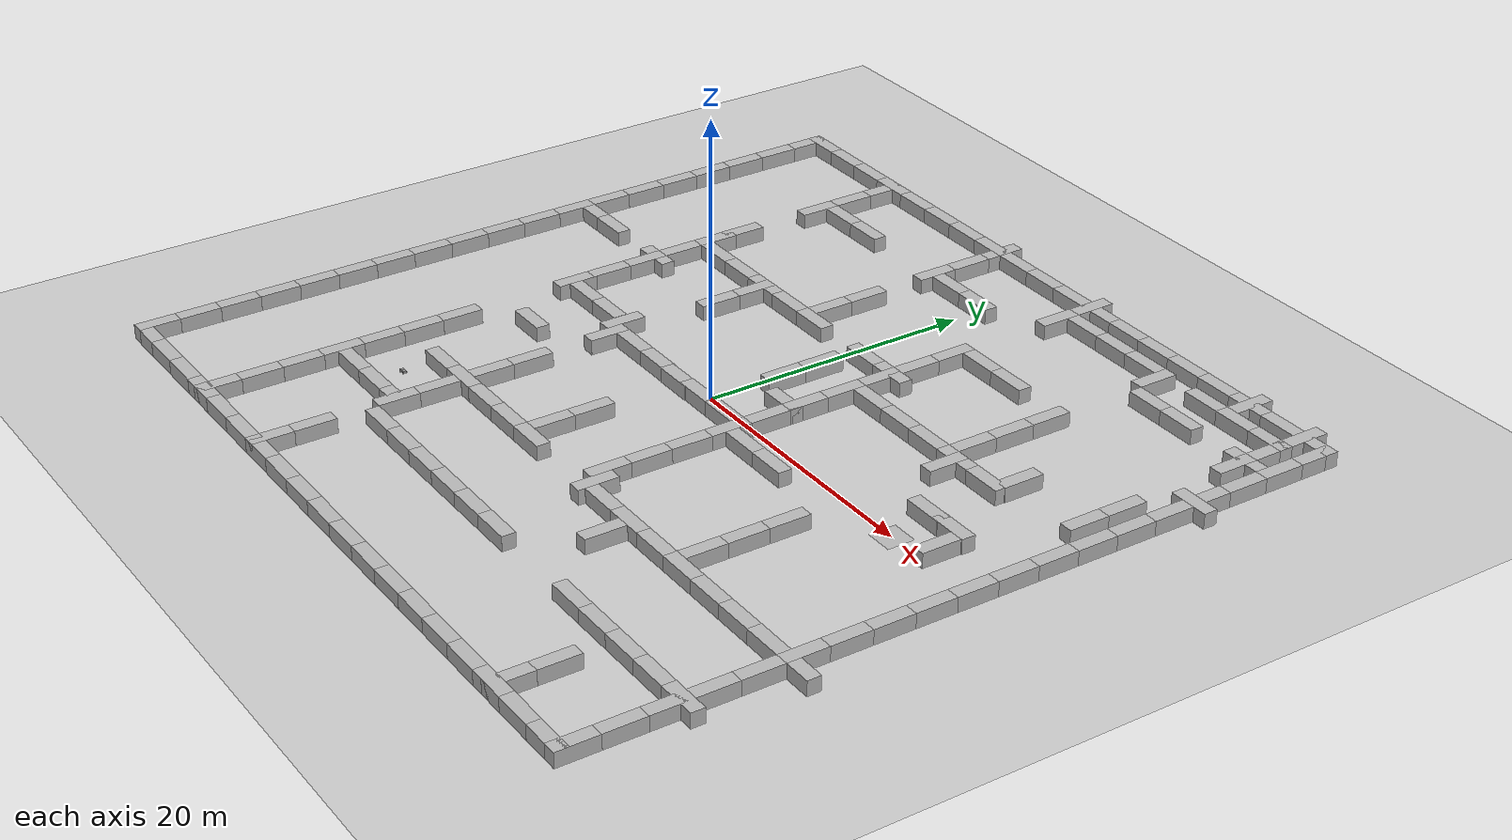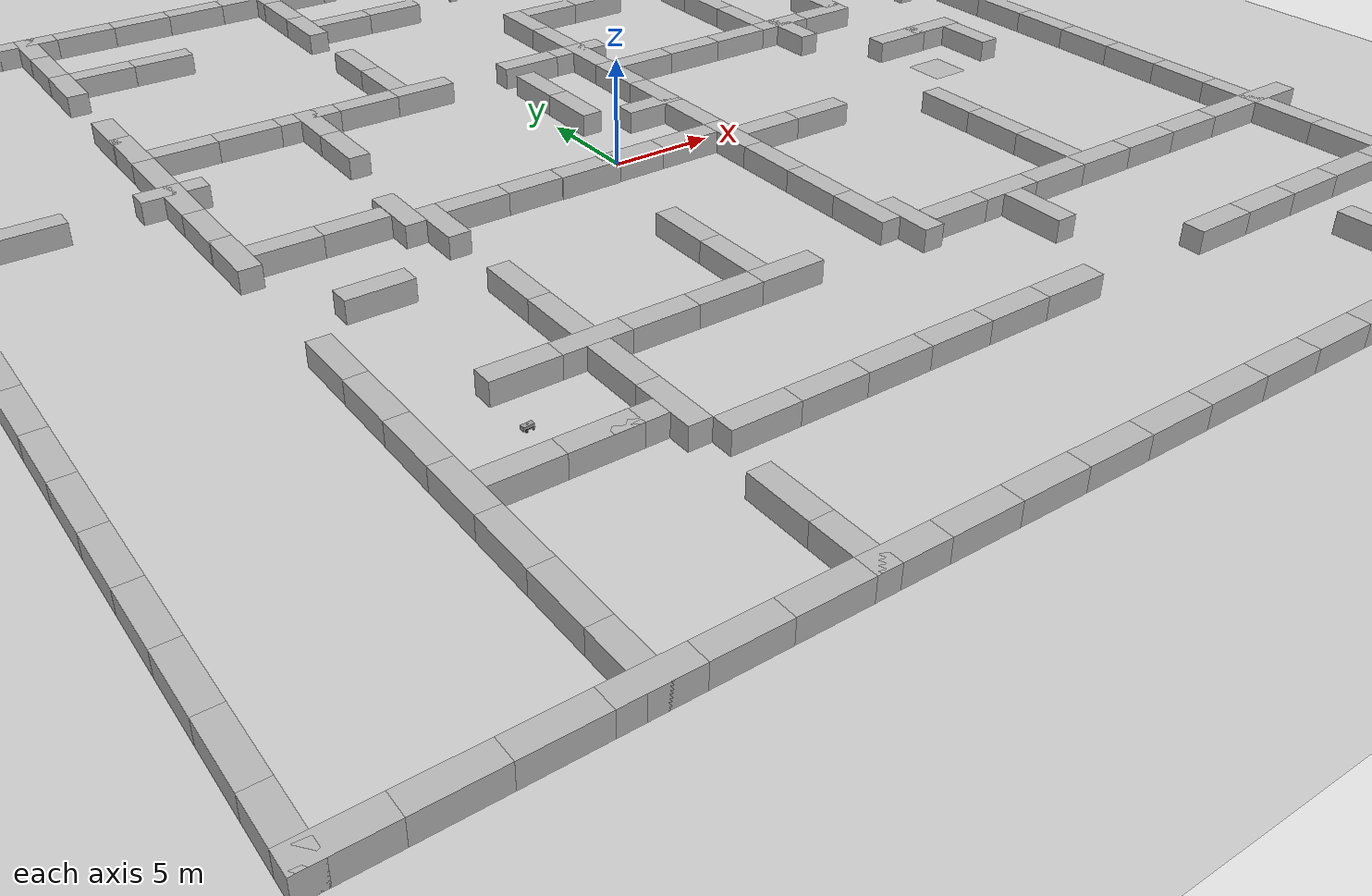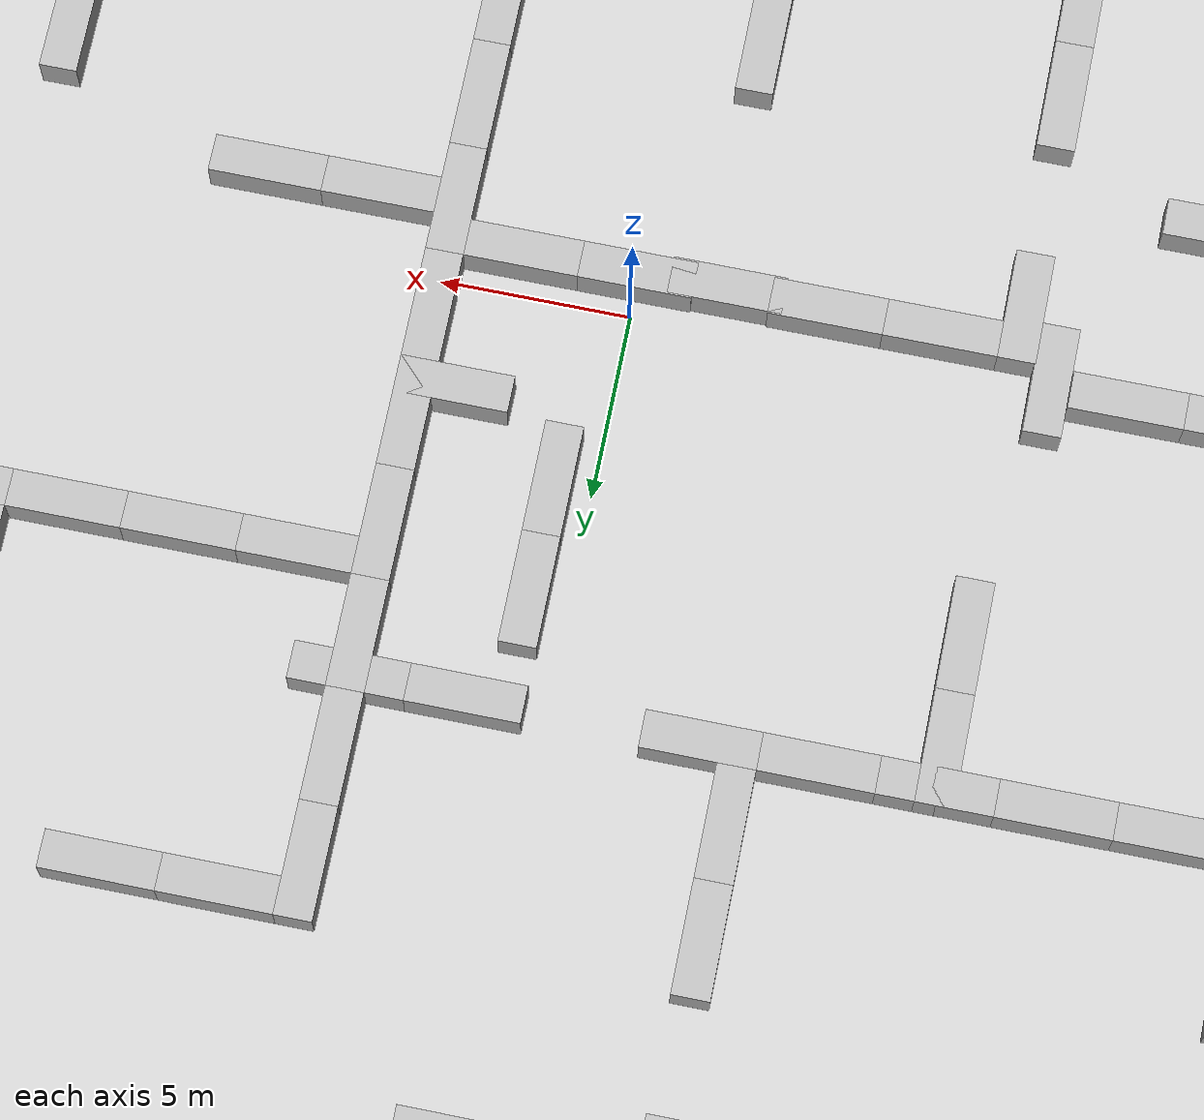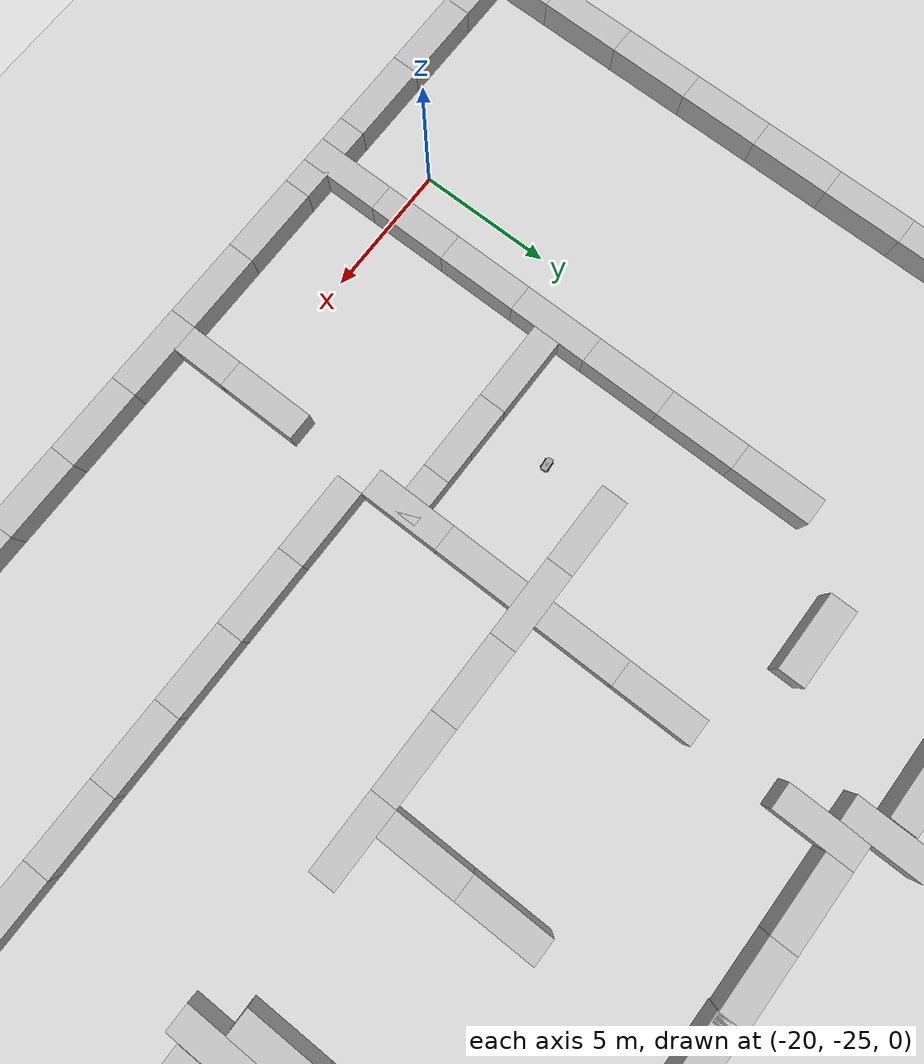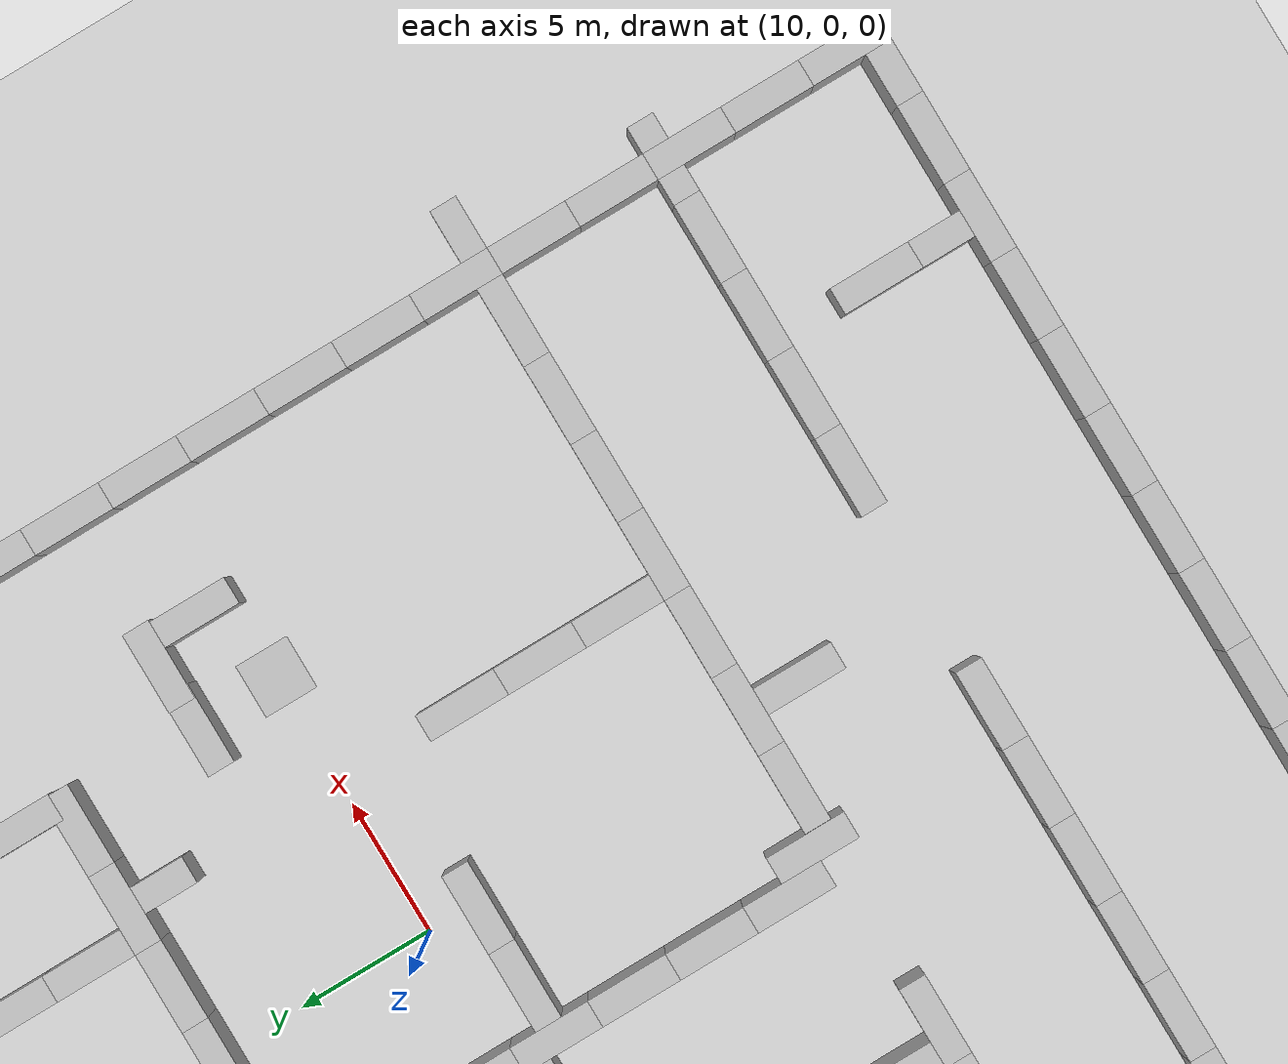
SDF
<sdf version="1.6">
 <world name="default">
  <light name="sun" type="directional">
   <pose>0 0 10 0 -0 0</pose>
   <diffuse>0.8 0.8 0.8 1</diffuse>
   <specular>0.2 0.2 0.2 1</specular>
   <attenuation>
    <range>1000</range>
    <constant>0.9</constant>
    <linear>0.01</linear>
    <quadratic>0.001</quadratic>
   </attenuation>
   <direction>-0.5 0.1 -0.9</direction>
  </light>
  <model name="ground_plane">
   <static>1</static>
   <link name="link">
    <collision name="collision">
     <geometry><plane><normal>0 0 1</normal><size>100 100</size></plane></geometry>
     <surface>
      <contact><collide_bitmask>65535</collide_bitmask></contact>
      <friction><ode><mu>100</mu><mu2>50</mu2></ode></friction>
     </surface>
    </collision>
    <visual name="visual">
     <cast_shadows>0</cast_shadows>
     <geometry><plane><normal>0 0 1</normal><size>100 100</size></plane></geometry>
     <material>
      <script><uri>file://media/materials/scripts/gazebo.material</uri><name>Gazebo/Grey</name></script>
     </material>
    </visual>
   </link>
  </model>
  <model name="goal">
   <static>1</static>
   <link name="link">
    <visual name="visual">
     <geometry><mesh><uri>model://checkerboard_plane/meshes/checkerboard_plane.dae</uri></mesh></geometry>
    </visual>
   </link>
   <pose>20 0 0.01 0 -0 0</pose>
  </model>
  <model name="wall0">
   <static>1</static>
   <link name="chassis">
    <pose>0 0 1.5 0 -0 0</pose>
    <collision name="collision"><geometry><box><size>3 1 3</size></box></geometry></collision>
    <visual name="visual">
     <geometry><mesh><uri>model://brick_box_3x1x3/meshes/simple_box.dae</uri><scale>3 1 3</scale></mesh></geometry>
     <material>
      <script>
       <uri>model://brick_box_3x1x3/materials/scripts</uri>
       <uri>model://brick_box_3x1x3/materials/textures</uri>
       <name>BrickBox/Diffuse</name>
      </script>
     </material>
    </visual>
   </link>
   <pose>-27 -28 -2 0 -0 0</pose>
  </model>
  <model name="wall1">
   <static>1</static>
   <link name="chassis">
    <pose>0 0 1.5 0 -0 0</pose>
    <collision name="collision"><geometry><box><size>3 1 3</size></box></geometry></collision>
    <visual name="visual">
     <geometry><mesh><uri>model://brick_box_3x1x3/meshes/simple_box.dae</uri><scale>3 1 3</scale></mesh></geometry>
     <material>
      <script>
       <uri>model://brick_box_3x1x3/materials/scripts</uri>
       <uri>model://brick_box_3x1x3/materials/textures</uri>
       <name>BrickBox/Diffuse</name>
      </script>
     </material>
    </visual>
   </link>
   <pose>-27 28 -2 0 -0 0</pose>
  </model>
  <model name="wall2">
   <static>1</static>
   <link name="chassis">
    <pose>0 0 1.5 0 -0 0</pose>
    <collision name="collision"><geometry><box><size>3 1 3</size></box></geometry></collision>
    <visual name="visual">
     <geometry><mesh><uri>model://brick_box_3x1x3/meshes/simple_box.dae</uri><scale>3 1 3</scale></mesh></geometry>
     <material>
      <script>
       <uri>model://brick_box_3x1x3/materials/scripts</uri>
       <uri>model://brick_box_3x1x3/materials/textures</uri>
       <name>BrickBox/Diffuse</name>
      </script>
     </material>
    </visual>
   </link>
   <pose>-28 -27 -2 0 -0 1.5708</pose>
  </model>
  <model name="wall3">
   <static>1</static>
   <link name="chassis">
    <pose>0 0 1.5 0 -0 0</pose>
    <collision name="collision"><geometry><box><size>3 1 3</size></box></geometry></collision>
    <visual name="visual">
     <geometry><mesh><uri>model://brick_box_3x1x3/meshes/simple_box.dae</uri><scale>3 1 3</scale></mesh></geometry>
     <material>
      <script>
       <uri>model://brick_box_3x1x3/materials/scripts</uri>
       <uri>model://brick_box_3x1x3/materials/textures</uri>
       <name>BrickBox/Diffuse</name>
      </script>
     </material>
    </visual>
   </link>
   <pose>28 -27 -2 0 -0 1.5708</pose>
  </model>
  <model name="wall4">
   <static>1</static>
   <link name="chassis">
    <pose>0 0 1.5 0 -0 0</pose>
    <collision name="collision"><geometry><box><size>3 1 3</size></box></geometry></collision>
    <visual name="visual">
     <geometry><mesh><uri>model://brick_box_3x1x3/meshes/simple_box.dae</uri><scale>3 1 3</scale></mesh></geometry>
     <material>
      <script>
       <uri>model://brick_box_3x1x3/materials/scripts</uri>
       <uri>model://brick_box_3x1x3/materials/textures</uri>
       <name>BrickBox/Diffuse</name>
      </script>
     </material>
    </visual>
   </link>
   <pose>-24 -28 -2 0 -0 0</pose>
  </model>
  <model name="wall5">
   <static>1</static>
   <link name="chassis">
    <pose>0 0 1.5 0 -0 0</pose>
    <collision name="collision"><geometry><box><size>3 1 3</size></box></geometry></collision>
    <visual name="visual">
     <geometry><mesh><uri>model://brick_box_3x1x3/meshes/simple_box.dae</uri><scale>3 1 3</scale></mesh></geometry>
     <material>
      <script>
       <uri>model://brick_box_3x1x3/materials/scripts</uri>
       <uri>model://brick_box_3x1x3/materials/textures</uri>
       <name>BrickBox/Diffuse</name>
      </script>
     </material>
    </visual>
   </link>
   <pose>-24 28 -2 0 -0 0</pose>
  </model>
  <model name="wall6">
   <static>1</static>
   <link name="chassis">
    <pose>0 0 1.5 0 -0 0</pose>
    <collision name="collision"><geometry><box><size>3 1 3</size></box></geometry></collision>
    <visual name="visual">
     <geometry><mesh><uri>model://brick_box_3x1x3/meshes/simple_box.dae</uri><scale>3 1 3</scale></mesh></geometry>
     <material>
      <script>
       <uri>model://brick_box_3x1x3/materials/scripts</uri>
       <uri>model://brick_box_3x1x3/materials/textures</uri>
       <name>BrickBox/Diffuse</name>
      </script>
     </material>
    </visual>
   </link>
   <pose>-28 -24 -2 0 -0 1.5708</pose>
  </model>
  <model name="wall7">
   <static>1</static>
   <link name="chassis">
    <pose>0 0 1.5 0 -0 0</pose>
    <collision name="collision"><geometry><box><size>3 1 3</size></box></geometry></collision>
    <visual name="visual">
     <geometry><mesh><uri>model://brick_box_3x1x3/meshes/simple_box.dae</uri><scale>3 1 3</scale></mesh></geometry>
     <material>
      <script>
       <uri>model://brick_box_3x1x3/materials/scripts</uri>
       <uri>model://brick_box_3x1x3/materials/textures</uri>
       <name>BrickBox/Diffuse</name>
      </script>
     </material>
    </visual>
   </link>
   <pose>28 -24 -2 0 -0 1.5708</pose>
  </model>
  <model name="wall8">
   <static>1</static>
   <link name="chassis">
    <pose>0 0 1.5 0 -0 0</pose>
    <collision name="collision"><geometry><box><size>3 1 3</size></box></geometry></collision>
    <visual name="visual">
     <geometry><mesh><uri>model://brick_box_3x1x3/meshes/simple_box.dae</uri><scale>3 1 3</scale></mesh></geometry>
     <material>
      <script>
       <uri>model://brick_box_3x1x3/materials/scripts</uri>
       <uri>model://brick_box_3x1x3/materials/textures</uri>
       <name>BrickBox/Diffuse</name>
      </script>
     </material>
    </visual>
   </link>
   <pose>-21 -28 -2 0 -0 0</pose>
  </model>
  <model name="wall9">
   <static>1</static>
   <link name="chassis">
    <pose>0 0 1.5 0 -0 0</pose>
    <collision name="collision"><geometry><box><size>3 1 3</size></box></geometry></collision>
    <visual name="visual">
     <geometry><mesh><uri>model://brick_box_3x1x3/meshes/simple_box.dae</uri><scale>3 1 3</scale></mesh></geometry>
     <material>
      <script>
       <uri>model://brick_box_3x1x3/materials/scripts</uri>
       <uri>model://brick_box_3x1x3/materials/textures</uri>
       <name>BrickBox/Diffuse</name>
      </script>
     </material>
    </visual>
   </link>
   <pose>-21 28 -2 0 -0 0</pose>
  </model>
  <model name="wall10">
   <static>1</static>
   <link name="chassis">
    <pose>0 0 1.5 0 -0 0</pose>
    <collision name="collision"><geometry><box><size>3 1 3</size></box></geometry></collision>
    <visual name="visual">
     <geometry><mesh><uri>model://brick_box_3x1x3/meshes/simple_box.dae</uri><scale>3 1 3</scale></mesh></geometry>
     <material>
      <script>
       <uri>model://brick_box_3x1x3/materials/scripts</uri>
       <uri>model://brick_box_3x1x3/materials/textures</uri>
       <name>BrickBox/Diffuse</name>
      </script>
     </material>
    </visual>
   </link>
   <pose>-28 -21 -2 0 -0 1.5708</pose>
  </model>
  <model name="wall11">
   <static>1</static>
   <link name="chassis">
    <pose>0 0 1.5 0 -0 0</pose>
    <collision name="collision"><geometry><box><size>3 1 3</size></box></geometry></collision>
    <visual name="visual">
     <geometry><mesh><uri>model://brick_box_3x1x3/meshes/simple_box.dae</uri><scale>3 1 3</scale></mesh></geometry>
     <material>
      <script>
       <uri>model://brick_box_3x1x3/materials/scripts</uri>
       <uri>model://brick_box_3x1x3/materials/textures</uri>
       <name>BrickBox/Diffuse</name>
      </script>
     </material>
    </visual>
   </link>
   <pose>28 -21 -2 0 -0 1.5708</pose>
  </model>
  <model name="wall12">
   <static>1</static>
   <link name="chassis">
    <pose>0 0 1.5 0 -0 0</pose>
    <collision name="collision"><geometry><box><size>3 1 3</size></box></geometry></collision>
    <visual name="visual">
     <geometry><mesh><uri>model://brick_box_3x1x3/meshes/simple_box.dae</uri><scale>3 1 3</scale></mesh></geometry>
     <material>
      <script>
       <uri>model://brick_box_3x1x3/materials/scripts</uri>
       <uri>model://brick_box_3x1x3/materials/textures</uri>
       <name>BrickBox/Diffuse</name>
      </script>
     </material>
    </visual>
   </link>
   <pose>-18 -28 -2 0 -0 0</pose>
  </model>
  <model name="wall13">
   <static>1</static>
   <link name="chassis">
    <pose>0 0 1.5 0 -0 0</pose>
    <collision name="collision"><geometry><box><size>3 1 3</size></box></geometry></collision>
    <visual name="visual">
     <geometry><mesh><uri>model://brick_box_3x1x3/meshes/simple_box.dae</uri><scale>3 1 3</scale></mesh></geometry>
     <material>
      <script>
       <uri>model://brick_box_3x1x3/materials/scripts</uri>
       <uri>model://brick_box_3x1x3/materials/textures</uri>
       <name>BrickBox/Diffuse</name>
      </script>
     </material>
    </visual>
   </link>
   <pose>-18 28 -2 0 -0 0</pose>
  </model>
  <model name="wall14">
   <static>1</static>
   <link name="chassis">
    <pose>0 0 1.5 0 -0 0</pose>
    <collision name="collision"><geometry><box><size>3 1 3</size></box></geometry></collision>
    <visual name="visual">
     <geometry><mesh><uri>model://brick_box_3x1x3/meshes/simple_box.dae</uri><scale>3 1 3</scale></mesh></geometry>
     <material>
      <script>
       <uri>model://brick_box_3x1x3/materials/scripts</uri>
       <uri>model://brick_box_3x1x3/materials/textures</uri>
       <name>BrickBox/Diffuse</name>
      </script>
     </material>
    </visual>
   </link>
   <pose>-28 -18 -2 0 -0 1.5708</pose>
  </model>
  <model name="wall15">
   <static>1</static>
   <link name="chassis">
    <pose>0 0 1.5 0 -0 0</pose>
    <collision name="collision"><geometry><box><size>3 1 3</size></box></geometry></collision>
    <visual name="visual">
     <geometry><mesh><uri>model://brick_box_3x1x3/meshes/simple_box.dae</uri><scale>3 1 3</scale></mesh></geometry>
     <material>
      <script>
       <uri>model://brick_box_3x1x3/materials/scripts</uri>
       <uri>model://brick_box_3x1x3/materials/textures</uri>
       <name>BrickBox/Diffuse</name>
      </script>
     </material>
    </visual>
   </link>
   <pose>28 -18 -2 0 -0 1.5708</pose>
  </model>
  <model name="wall16">
   <static>1</static>
   <link name="chassis">
    <pose>0 0 1.5 0 -0 0</pose>
    <collision name="collision"><geometry><box><size>3 1 3</size></box></geometry></collision>
    <visual name="visual">
     <geometry><mesh><uri>model://brick_box_3x1x3/meshes/simple_box.dae</uri><scale>3 1 3</scale></mesh></geometry>
     <material>
      <script>
       <uri>model://brick_box_3x1x3/materials/scripts</uri>
       <uri>model://brick_box_3x1x3/materials/textures</uri>
       <name>BrickBox/Diffuse</name>
      </script>
     </material>
    </visual>
   </link>
   <pose>-15 -28 -2 0 -0 0</pose>
  </model>
  <model name="wall17">
   <static>1</static>
   <link name="chassis">
    <pose>0 0 1.5 0 -0 0</pose>
    <collision name="collision"><geometry><box><size>3 1 3</size></box></geometry></collision>
    <visual name="visual">
     <geometry><mesh><uri>model://brick_box_3x1x3/meshes/simple_box.dae</uri><scale>3 1 3</scale></mesh></geometry>
     <material>
      <script>
       <uri>model://brick_box_3x1x3/materials/scripts</uri>
       <uri>model://brick_box_3x1x3/materials/textures</uri>
       <name>BrickBox/Diffuse</name>
      </script>
     </material>
    </visual>
   </link>
   <pose>-15 28 -2 0 -0 0</pose>
  </model>
  <model name="wall18">
   <static>1</static>
   <link name="chassis">
    <pose>0 0 1.5 0 -0 0</pose>
    <collision name="collision"><geometry><box><size>3 1 3</size></box></geometry></collision>
    <visual name="visual">
     <geometry><mesh><uri>model://brick_box_3x1x3/meshes/simple_box.dae</uri><scale>3 1 3</scale></mesh></geometry>
     <material>
      <script>
       <uri>model://brick_box_3x1x3/materials/scripts</uri>
       <uri>model://brick_box_3x1x3/materials/textures</uri>
       <name>BrickBox/Diffuse</name>
      </script>
     </material>
    </visual>
   </link>
   <pose>-28 -15 -2 0 -0 1.5708</pose>
  </model>
  <model name="wall19">
   <static>1</static>
   <link name="chassis">
    <pose>0 0 1.5 0 -0 0</pose>
    <collision name="collision"><geometry><box><size>3 1 3</size></box></geometry></collision>
    <visual name="visual">
     <geometry><mesh><uri>model://brick_box_3x1x3/meshes/simple_box.dae</uri><scale>3 1 3</scale></mesh></geometry>
     <material>
      <script>
       <uri>model://brick_box_3x1x3/materials/scripts</uri>
       <uri>model://brick_box_3x1x3/materials/textures</uri>
       <name>BrickBox/Diffuse</name>
      </script>
     </material>
    </visual>
   </link>
   <pose>28 -15 -2 0 -0 1.5708</pose>
  </model>
  <model name="wall20">
   <static>1</static>
   <link name="chassis">
    <pose>0 0 1.5 0 -0 0</pose>
    <collision name="collision"><geometry><box><size>3 1 3</size></box></geometry></collision>
    <visual name="visual">
     <geometry><mesh><uri>model://brick_box_3x1x3/meshes/simple_box.dae</uri><scale>3 1 3</scale></mesh></geometry>
     <material>
      <script>
       <uri>model://brick_box_3x1x3/materials/scripts</uri>
       <uri>model://brick_box_3x1x3/materials/textures</uri>
       <name>BrickBox/Diffuse</name>
      </script>
     </material>
    </visual>
   </link>
   <pose>-12 -28 -2 0 -0 0</pose>
  </model>
  <model name="wall21">
   <static>1</static>
   <link name="chassis">
    <pose>0 0 1.5 0 -0 0</pose>
    <collision name="collision"><geometry><box><size>3 1 3</size></box></geometry></collision>
    <visual name="visual">
     <geometry><mesh><uri>model://brick_box_3x1x3/meshes/simple_box.dae</uri><scale>3 1 3</scale></mesh></geometry>
     <material>
      <script>
       <uri>model://brick_box_3x1x3/materials/scripts</uri>
       <uri>model://brick_box_3x1x3/materials/textures</uri>
       <name>BrickBox/Diffuse</name>
      </script>
     </material>
    </visual>
   </link>
   <pose>-12 28 -2 0 -0 0</pose>
  </model>
  <model name="wall22">
   <static>1</static>
   <link name="chassis">
    <pose>0 0 1.5 0 -0 0</pose>
    <collision name="collision"><geometry><box><size>3 1 3</size></box></geometry></collision>
    <visual name="visual">
     <geometry><mesh><uri>model://brick_box_3x1x3/meshes/simple_box.dae</uri><scale>3 1 3</scale></mesh></geometry>
     <material>
      <script>
       <uri>model://brick_box_3x1x3/materials/scripts</uri>
       <uri>model://brick_box_3x1x3/materials/textures</uri>
       <name>BrickBox/Diffuse</name>
      </script>
     </material>
    </visual>
   </link>
   <pose>-28 -12 -2 0 -0 1.5708</pose>
  </model>
  <model name="wall23">
   <static>1</static>
   <link name="chassis">
    <pose>0 0 1.5 0 -0 0</pose>
    <collision name="collision"><geometry><box><size>3 1 3</size></box></geometry></collision>
    <visual name="visual">
     <geometry><mesh><uri>model://brick_box_3x1x3/meshes/simple_box.dae</uri><scale>3 1 3</scale></mesh></geometry>
     <material>
      <script>
       <uri>model://brick_box_3x1x3/materials/scripts</uri>
       <uri>model://brick_box_3x1x3/materials/textures</uri>
       <name>BrickBox/Diffuse</name>
      </script>
     </material>
    </visual>
   </link>
   <pose>28 -12 -2 0 -0 1.5708</pose>
  </model>
  <model name="wall24">
   <static>1</static>
   <link name="chassis">
    <pose>0 0 1.5 0 -0 0</pose>
    <collision name="collision"><geometry><box><size>3 1 3</size></box></geometry></collision>
    <visual name="visual">
     <geometry><mesh><uri>model://brick_box_3x1x3/meshes/simple_box.dae</uri><scale>3 1 3</scale></mesh></geometry>
     <material>
      <script>
       <uri>model://brick_box_3x1x3/materials/scripts</uri>
       <uri>model://brick_box_3x1x3/materials/textures</uri>
       <name>BrickBox/Diffuse</name>
      </script>
     </material>
    </visual>
   </link>
   <pose>-9 -28 -2 0 -0 0</pose>
  </model>
  <model name="wall25">
   <static>1</static>
   <link name="chassis">
    <pose>0 0 1.5 0 -0 0</pose>
    <collision name="collision"><geometry><box><size>3 1 3</size></box></geometry></collision>
    <visual name="visual">
     <geometry><mesh><uri>model://brick_box_3x1x3/meshes/simple_box.dae</uri><scale>3 1 3</scale></mesh></geometry>
     <material>
      <script>
       <uri>model://brick_box_3x1x3/materials/scripts</uri>
       <uri>model://brick_box_3x1x3/materials/textures</uri>
       <name>BrickBox/Diffuse</name>
      </script>
     </material>
    </visual>
   </link>
   <pose>-9 28 -2 0 -0 0</pose>
  </model>
  <model name="wall26">
   <static>1</static>
   <link name="chassis">
    <pose>0 0 1.5 0 -0 0</pose>
    <collision name="collision"><geometry><box><size>3 1 3</size></box></geometry></collision>
    <visual name="visual">
     <geometry><mesh><uri>model://brick_box_3x1x3/meshes/simple_box.dae</uri><scale>3 1 3</scale></mesh></geometry>
     <material>
      <script>
       <uri>model://brick_box_3x1x3/materials/scripts</uri>
       <uri>model://brick_box_3x1x3/materials/textures</uri>
       <name>BrickBox/Diffuse</name>
      </script>
     </material>
    </visual>
   </link>
   <pose>-28 -9 -2 0 -0 1.5708</pose>
  </model>
  <model name="wall27">
   <static>1</static>
   <link name="chassis">
    <pose>0 0 1.5 0 -0 0</pose>
    <collision name="collision"><geometry><box><size>3 1 3</size></box></geometry></collision>
    <visual name="visual">
     <geometry><mesh><uri>model://brick_box_3x1x3/meshes/simple_box.dae</uri><scale>3 1 3</scale></mesh></geometry>
     <material>
      <script>
       <uri>model://brick_box_3x1x3/materials/scripts</uri>
       <uri>model://brick_box_3x1x3/materials/textures</uri>
       <name>BrickBox/Diffuse</name>
      </script>
     </material>
    </visual>
   </link>
   <pose>28 -9 -2 0 -0 1.5708</pose>
  </model>
  <model name="wall28">
   <static>1</static>
   <link name="chassis">
    <pose>0 0 1.5 0 -0 0</pose>
    <collision name="collision"><geometry><box><size>3 1 3</size></box></geometry></collision>
    <visual name="visual">
     <geometry><mesh><uri>model://brick_box_3x1x3/meshes/simple_box.dae</uri><scale>3 1 3</scale></mesh></geometry>
     <material>
      <script>
       <uri>model://brick_box_3x1x3/materials/scripts</uri>
       <uri>model://brick_box_3x1x3/materials/textures</uri>
       <name>BrickBox/Diffuse</name>
      </script>
     </material>
    </visual>
   </link>
   <pose>-6 -28 -2 0 -0 0</pose>
  </model>
  <model name="wall29">
   <static>1</static>
   <link name="chassis">
    <pose>0 0 1.5 0 -0 0</pose>
    <collision name="collision"><geometry><box><size>3 1 3</size></box></geometry></collision>
    <visual name="visual">
     <geometry><mesh><uri>model://brick_box_3x1x3/meshes/simple_box.dae</uri><scale>3 1 3</scale></mesh></geometry>
     <material>
      <script>
       <uri>model://brick_box_3x1x3/materials/scripts</uri>
       <uri>model://brick_box_3x1x3/materials/textures</uri>
       <name>BrickBox/Diffuse</name>
      </script>
     </material>
    </visual>
   </link>
   <pose>-6 28 -2 0 -0 0</pose>
  </model>
  <model name="wall30">
   <static>1</static>
   <link name="chassis">
    <pose>0 0 1.5 0 -0 0</pose>
    <collision name="collision"><geometry><box><size>3 1 3</size></box></geometry></collision>
    <visual name="visual">
     <geometry><mesh><uri>model://brick_box_3x1x3/meshes/simple_box.dae</uri><scale>3 1 3</scale></mesh></geometry>
     <material>
      <script>
       <uri>model://brick_box_3x1x3/materials/scripts</uri>
       <uri>model://brick_box_3x1x3/materials/textures</uri>
       <name>BrickBox/Diffuse</name>
      </script>
     </material>
    </visual>
   </link>
   <pose>-28 -6 -2 0 -0 1.5708</pose>
  </model>
  <model name="wall31">
   <static>1</static>
   <link name="chassis">
    <pose>0 0 1.5 0 -0 0</pose>
    <collision name="collision"><geometry><box><size>3 1 3</size></box></geometry></collision>
    <visual name="visual">
     <geometry><mesh><uri>model://brick_box_3x1x3/meshes/simple_box.dae</uri><scale>3 1 3</scale></mesh></geometry>
     <material>
      <script>
       <uri>model://brick_box_3x1x3/materials/scripts</uri>
       <uri>model://brick_box_3x1x3/materials/textures</uri>
       <name>BrickBox/Diffuse</name>
      </script>
     </material>
    </visual>
   </link>
   <pose>28 -6 -2 0 -0 1.5708</pose>
  </model>
  <model name="wall32">
   <static>1</static>
   <link name="chassis">
    <pose>0 0 1.5 0 -0 0</pose>
    <collision name="collision"><geometry><box><size>3 1 3</size></box></geometry></collision>
    <visual name="visual">
     <geometry><mesh><uri>model://brick_box_3x1x3/meshes/simple_box.dae</uri><scale>3 1 3</scale></mesh></geometry>
     <material>
      <script>
       <uri>model://brick_box_3x1x3/materials/scripts</uri>
       <uri>model://brick_box_3x1x3/materials/textures</uri>
       <name>BrickBox/Diffuse</name>
      </script>
     </material>
    </visual>
   </link>
   <pose>-3 -28 -2 0 -0 0</pose>
  </model>
  <model name="wall33">
   <static>1</static>
   <link name="chassis">
    <pose>0 0 1.5 0 -0 0</pose>
    <collision name="collision"><geometry><box><size>3 1 3</size></box></geometry></collision>
    <visual name="visual">
     <geometry><mesh><uri>model://brick_box_3x1x3/meshes/simple_box.dae</uri><scale>3 1 3</scale></mesh></geometry>
     <material>
      <script>
       <uri>model://brick_box_3x1x3/materials/scripts</uri>
       <uri>model://brick_box_3x1x3/materials/textures</uri>
       <name>BrickBox/Diffuse</name>
      </script>
     </material>
    </visual>
   </link>
   <pose>-3 28 -2 0 -0 0</pose>
  </model>
  <model name="wall34">
   <static>1</static>
   <link name="chassis">
    <pose>0 0 1.5 0 -0 0</pose>
    <collision name="collision"><geometry><box><size>3 1 3</size></box></geometry></collision>
    <visual name="visual">
     <geometry><mesh><uri>model://brick_box_3x1x3/meshes/simple_box.dae</uri><scale>3 1 3</scale></mesh></geometry>
     <material>
      <script>
       <uri>model://brick_box_3x1x3/materials/scripts</uri>
       <uri>model://brick_box_3x1x3/materials/textures</uri>
       <name>BrickBox/Diffuse</name>
      </script>
     </material>
    </visual>
   </link>
   <pose>-28 -3 -2 0 -0 1.5708</pose>
  </model>
  <model name="wall35">
   <static>1</static>
   <link name="chassis">
    <pose>0 0 1.5 0 -0 0</pose>
    <collision name="collision"><geometry><box><size>3 1 3</size></box></geometry></collision>
    <visual name="visual">
     <geometry><mesh><uri>model://brick_box_3x1x3/meshes/simple_box.dae</uri><scale>3 1 3</scale></mesh></geometry>
     <material>
      <script>
       <uri>model://brick_box_3x1x3/materials/scripts</uri>
       <uri>model://brick_box_3x1x3/materials/textures</uri>
       <name>BrickBox/Diffuse</name>
      </script>
     </material>
    </visual>
   </link>
   <pose>28 -3 -2 0 -0 1.5708</pose>
  </model>
  <model name="wall36">
   <static>1</static>
   <link name="chassis">
    <pose>0 0 1.5 0 -0 0</pose>
    <collision name="collision"><geometry><box><size>3 1 3</size></box></geometry></collision>
    <visual name="visual">
     <geometry><mesh><uri>model://brick_box_3x1x3/meshes/simple_box.dae</uri><scale>3 1 3</scale></mesh></geometry>
     <material>
      <script>
       <uri>model://brick_box_3x1x3/materials/scripts</uri>
       <uri>model://brick_box_3x1x3/materials/textures</uri>
       <name>BrickBox/Diffuse</name>
      </script>
     </material>
    </visual>
   </link>
   <pose>0 -28 -2 0 -0 0</pose>
  </model>
  <model name="wall37">
   <static>1</static>
   <link name="chassis">
    <pose>0 0 1.5 0 -0 0</pose>
    <collision name="collision"><geometry><box><size>3 1 3</size></box></geometry></collision>
    <visual name="visual">
     <geometry><mesh><uri>model://brick_box_3x1x3/meshes/simple_box.dae</uri><scale>3 1 3</scale></mesh></geometry>
     <material>
      <script>
       <uri>model://brick_box_3x1x3/materials/scripts</uri>
       <uri>model://brick_box_3x1x3/materials/textures</uri>
       <name>BrickBox/Diffuse</name>
      </script>
     </material>
    </visual>
   </link>
   <pose>0 28 -2 0 -0 0</pose>
  </model>
  <model name="wall38">
   <static>1</static>
   <link name="chassis">
    <pose>0 0 1.5 0 -0 0</pose>
    <collision name="collision"><geometry><box><size>3 1 3</size></box></geometry></collision>
    <visual name="visual">
     <geometry><mesh><uri>model://brick_box_3x1x3/meshes/simple_box.dae</uri><scale>3 1 3</scale></mesh></geometry>
     <material>
      <script>
       <uri>model://brick_box_3x1x3/materials/scripts</uri>
       <uri>model://brick_box_3x1x3/materials/textures</uri>
       <name>BrickBox/Diffuse</name>
      </script>
     </material>
    </visual>
   </link>
   <pose>-28 0 -2 0 -0 1.5708</pose>
  </model>
  <model name="wall39">
   <static>1</static>
   <link name="chassis">
    <pose>0 0 1.5 0 -0 0</pose>
    <collision name="collision"><geometry><box><size>3 1 3</size></box></geometry></collision>
    <visual name="visual">
     <geometry><mesh><uri>model://brick_box_3x1x3/meshes/simple_box.dae</uri><scale>3 1 3</scale></mesh></geometry>
     <material>
      <script>
       <uri>model://brick_box_3x1x3/materials/scripts</uri>
       <uri>model://brick_box_3x1x3/materials/textures</uri>
       <name>BrickBox/Diffuse</name>
      </script>
     </material>
    </visual>
   </link>
   <pose>28 0 -2 0 -0 1.5708</pose>
  </model>
  <model name="wall40">
   <static>1</static>
   <link name="chassis">
    <pose>0 0 1.5 0 -0 0</pose>
    <collision name="collision"><geometry><box><size>3 1 3</size></box></geometry></collision>
    <visual name="visual">
     <geometry><mesh><uri>model://brick_box_3x1x3/meshes/simple_box.dae</uri><scale>3 1 3</scale></mesh></geometry>
     <material>
      <script>
       <uri>model://brick_box_3x1x3/materials/scripts</uri>
       <uri>model://brick_box_3x1x3/materials/textures</uri>
       <name>BrickBox/Diffuse</name>
      </script>
     </material>
    </visual>
   </link>
   <pose>3 -28 -2 0 -0 0</pose>
  </model>
  <model name="wall41">
   <static>1</static>
   <link name="chassis">
    <pose>0 0 1.5 0 -0 0</pose>
    <collision name="collision"><geometry><box><size>3 1 3</size></box></geometry></collision>
    <visual name="visual">
     <geometry><mesh><uri>model://brick_box_3x1x3/meshes/simple_box.dae</uri><scale>3 1 3</scale></mesh></geometry>
     <material>
      <script>
       <uri>model://brick_box_3x1x3/materials/scripts</uri>
       <uri>model://brick_box_3x1x3/materials/textures</uri>
       <name>BrickBox/Diffuse</name>
      </script>
     </material>
    </visual>
   </link>
   <pose>3 28 -2 0 -0 0</pose>
  </model>
  <model name="wall42">
   <static>1</static>
   <link name="chassis">
    <pose>0 0 1.5 0 -0 0</pose>
    <collision name="collision"><geometry><box><size>3 1 3</size></box></geometry></collision>
    <visual name="visual">
     <geometry><mesh><uri>model://brick_box_3x1x3/meshes/simple_box.dae</uri><scale>3 1 3</scale></mesh></geometry>
     <material>
      <script>
       <uri>model://brick_box_3x1x3/materials/scripts</uri>
       <uri>model://brick_box_3x1x3/materials/textures</uri>
       <name>BrickBox/Diffuse</name>
      </script>
     </material>
    </visual>
   </link>
   <pose>-28 3 -2 0 -0 1.5708</pose>
  </model>
  <model name="wall43">
   <static>1</static>
   <link name="chassis">
    <pose>0 0 1.5 0 -0 0</pose>
    <collision name="collision"><geometry><box><size>3 1 3</size></box></geometry></collision>
    <visual name="visual">
     <geometry><mesh><uri>model://brick_box_3x1x3/meshes/simple_box.dae</uri><scale>3 1 3</scale></mesh></geometry>
     <material>
      <script>
       <uri>model://brick_box_3x1x3/materials/scripts</uri>
       <uri>model://brick_box_3x1x3/materials/textures</uri>
       <name>BrickBox/Diffuse</name>
      </script>
     </material>
    </visual>
   </link>
   <pose>28 3 -2 0 -0 1.5708</pose>
  </model>
  <model name="wall44">
   <static>1</static>
   <link name="chassis">
    <pose>0 0 1.5 0 -0 0</pose>
    <collision name="collision"><geometry><box><size>3 1 3</size></box></geometry></collision>
    <visual name="visual">
     <geometry><mesh><uri>model://brick_box_3x1x3/meshes/simple_box.dae</uri><scale>3 1 3</scale></mesh></geometry>
     <material>
      <script>
       <uri>model://brick_box_3x1x3/materials/scripts</uri>
       <uri>model://brick_box_3x1x3/materials/textures</uri>
       <name>BrickBox/Diffuse</name>
      </script>
     </material>
    </visual>
   </link>
   <pose>6 -28 -2 0 -0 0</pose>
  </model>
  <model name="wall45">
   <static>1</static>
   <link name="chassis">
    <pose>0 0 1.5 0 -0 0</pose>
    <collision name="collision"><geometry><box><size>3 1 3</size></box></geometry></collision>
    <visual name="visual">
     <geometry><mesh><uri>model://brick_box_3x1x3/meshes/simple_box.dae</uri><scale>3 1 3</scale></mesh></geometry>
     <material>
      <script>
       <uri>model://brick_box_3x1x3/materials/scripts</uri>
       <uri>model://brick_box_3x1x3/materials/textures</uri>
       <name>BrickBox/Diffuse</name>
      </script>
     </material>
    </visual>
   </link>
   <pose>6 28 -2 0 -0 0</pose>
  </model>
  <model name="wall46">
   <static>1</static>
   <link name="chassis">
    <pose>0 0 1.5 0 -0 0</pose>
    <collision name="collision"><geometry><box><size>3 1 3</size></box></geometry></collision>
    <visual name="visual">
     <geometry><mesh><uri>model://brick_box_3x1x3/meshes/simple_box.dae</uri><scale>3 1 3</scale></mesh></geometry>
     <material>
      <script>
       <uri>model://brick_box_3x1x3/materials/scripts</uri>
       <uri>model://brick_box_3x1x3/materials/textures</uri>
       <name>BrickBox/Diffuse</name>
      </script>
     </material>
    </visual>
   </link>
   <pose>-28 6 -2 0 -0 1.5708</pose>
  </model>
  <model name="wall47">
   <static>1</static>
   <link name="chassis">
    <pose>0 0 1.5 0 -0 0</pose>
    <collision name="collision"><geometry><box><size>3 1 3</size></box></geometry></collision>
    <visual name="visual">
     <geometry><mesh><uri>model://brick_box_3x1x3/meshes/simple_box.dae</uri><scale>3 1 3</scale></mesh></geometry>
     <material>
      <script>
       <uri>model://brick_box_3x1x3/materials/scripts</uri>
       <uri>model://brick_box_3x1x3/materials/textures</uri>
       <name>BrickBox/Diffuse</name>
      </script>
     </material>
    </visual>
   </link>
   <pose>28 6 -2 0 -0 1.5708</pose>
  </model>
  <model name="wall48">
   <static>1</static>
   <link name="chassis">
    <pose>0 0 1.5 0 -0 0</pose>
    <collision name="collision"><geometry><box><size>3 1 3</size></box></geometry></collision>
    <visual name="visual">
     <geometry><mesh><uri>model://brick_box_3x1x3/meshes/simple_box.dae</uri><scale>3 1 3</scale></mesh></geometry>
     <material>
      <script>
       <uri>model://brick_box_3x1x3/materials/scripts</uri>
       <uri>model://brick_box_3x1x3/materials/textures</uri>
       <name>BrickBox/Diffuse</name>
      </script>
     </material>
    </visual>
   </link>
   <pose>9 -28 -2 0 -0 0</pose>
  </model>
  <model name="wall49">
   <static>1</static>
   <link name="chassis">
    <pose>0 0 1.5 0 -0 0</pose>
    <collision name="collision"><geometry><box><size>3 1 3</size></box></geometry></collision>
    <visual name="visual">
     <geometry><mesh><uri>model://brick_box_3x1x3/meshes/simple_box.dae</uri><scale>3 1 3</scale></mesh></geometry>
     <material>
      <script>
       <uri>model://brick_box_3x1x3/materials/scripts</uri>
       <uri>model://brick_box_3x1x3/materials/textures</uri>
       <name>BrickBox/Diffuse</name>
      </script>
     </material>
    </visual>
   </link>
   <pose>9 28 -2 0 -0 0</pose>
  </model>
  <model name="wall50">
   <static>1</static>
   <link name="chassis">
    <pose>0 0 1.5 0 -0 0</pose>
    <collision name="collision"><geometry><box><size>3 1 3</size></box></geometry></collision>
    <visual name="visual">
     <geometry><mesh><uri>model://brick_box_3x1x3/meshes/simple_box.dae</uri><scale>3 1 3</scale></mesh></geometry>
     <material>
      <script>
       <uri>model://brick_box_3x1x3/materials/scripts</uri>
       <uri>model://brick_box_3x1x3/materials/textures</uri>
       <name>BrickBox/Diffuse</name>
      </script>
     </material>
    </visual>
   </link>
   <pose>-28 9 -2 0 -0 1.5708</pose>
  </model>
  <model name="wall51">
   <static>1</static>
   <link name="chassis">
    <pose>0 0 1.5 0 -0 0</pose>
    <collision name="collision"><geometry><box><size>3 1 3</size></box></geometry></collision>
    <visual name="visual">
     <geometry><mesh><uri>model://brick_box_3x1x3/meshes/simple_box.dae</uri><scale>3 1 3</scale></mesh></geometry>
     <material>
      <script>
       <uri>model://brick_box_3x1x3/materials/scripts</uri>
       <uri>model://brick_box_3x1x3/materials/textures</uri>
       <name>BrickBox/Diffuse</name>
      </script>
     </material>
    </visual>
   </link>
   <pose>28 9 -2 0 -0 1.5708</pose>
  </model>
  <model name="wall52">
   <static>1</static>
   <link name="chassis">
    <pose>0 0 1.5 0 -0 0</pose>
    <collision name="collision"><geometry><box><size>3 1 3</size></box></geometry></collision>
    <visual name="visual">
     <geometry><mesh><uri>model://brick_box_3x1x3/meshes/simple_box.dae</uri><scale>3 1 3</scale></mesh></geometry>
     <material>
      <script>
       <uri>model://brick_box_3x1x3/materials/scripts</uri>
       <uri>model://brick_box_3x1x3/materials/textures</uri>
       <name>BrickBox/Diffuse</name>
      </script>
     </material>
    </visual>
   </link>
   <pose>12 -28 -2 0 -0 0</pose>
  </model>
  <model name="wall53">
   <static>1</static>
   <link name="chassis">
    <pose>0 0 1.5 0 -0 0</pose>
    <collision name="collision"><geometry><box><size>3 1 3</size></box></geometry></collision>
    <visual name="visual">
     <geometry><mesh><uri>model://brick_box_3x1x3/meshes/simple_box.dae</uri><scale>3 1 3</scale></mesh></geometry>
     <material>
      <script>
       <uri>model://brick_box_3x1x3/materials/scripts</uri>
       <uri>model://brick_box_3x1x3/materials/textures</uri>
       <name>BrickBox/Diffuse</name>
      </script>
     </material>
    </visual>
   </link>
   <pose>12 28 -2 0 -0 0</pose>
  </model>
  <model name="wall54">
   <static>1</static>
   <link name="chassis">
    <pose>0 0 1.5 0 -0 0</pose>
    <collision name="collision"><geometry><box><size>3 1 3</size></box></geometry></collision>
    <visual name="visual">
     <geometry><mesh><uri>model://brick_box_3x1x3/meshes/simple_box.dae</uri><scale>3 1 3</scale></mesh></geometry>
     <material>
      <script>
       <uri>model://brick_box_3x1x3/materials/scripts</uri>
       <uri>model://brick_box_3x1x3/materials/textures</uri>
       <name>BrickBox/Diffuse</name>
      </script>
     </material>
    </visual>
   </link>
   <pose>-28 12 -2 0 -0 1.5708</pose>
  </model>
  <model name="wall55">
   <static>1</static>
   <link name="chassis">
    <pose>0 0 1.5 0 -0 0</pose>
    <collision name="collision"><geometry><box><size>3 1 3</size></box></geometry></collision>
    <visual name="visual">
     <geometry><mesh><uri>model://brick_box_3x1x3/meshes/simple_box.dae</uri><scale>3 1 3</scale></mesh></geometry>
     <material>
      <script>
       <uri>model://brick_box_3x1x3/materials/scripts</uri>
       <uri>model://brick_box_3x1x3/materials/textures</uri>
       <name>BrickBox/Diffuse</name>
      </script>
     </material>
    </visual>
   </link>
   <pose>28 12 -2 0 -0 1.5708</pose>
  </model>
  <model name="wall56">
   <static>1</static>
   <link name="chassis">
    <pose>0 0 1.5 0 -0 0</pose>
    <collision name="collision"><geometry><box><size>3 1 3</size></box></geometry></collision>
    <visual name="visual">
     <geometry><mesh><uri>model://brick_box_3x1x3/meshes/simple_box.dae</uri><scale>3 1 3</scale></mesh></geometry>
     <material>
      <script>
       <uri>model://brick_box_3x1x3/materials/scripts</uri>
       <uri>model://brick_box_3x1x3/materials/textures</uri>
       <name>BrickBox/Diffuse</name>
      </script>
     </material>
    </visual>
   </link>
   <pose>15 -28 -2 0 -0 0</pose>
  </model>
  <model name="wall57">
   <static>1</static>
   <link name="chassis">
    <pose>0 0 1.5 0 -0 0</pose>
    <collision name="collision"><geometry><box><size>3 1 3</size></box></geometry></collision>
    <visual name="visual">
     <geometry><mesh><uri>model://brick_box_3x1x3/meshes/simple_box.dae</uri><scale>3 1 3</scale></mesh></geometry>
     <material>
      <script>
       <uri>model://brick_box_3x1x3/materials/scripts</uri>
       <uri>model://brick_box_3x1x3/materials/textures</uri>
       <name>BrickBox/Diffuse</name>
      </script>
     </material>
    </visual>
   </link>
   <pose>15 28 -2 0 -0 0</pose>
  </model>
  <model name="wall58">
   <static>1</static>
   <link name="chassis">
    <pose>0 0 1.5 0 -0 0</pose>
    <collision name="collision"><geometry><box><size>3 1 3</size></box></geometry></collision>
    <visual name="visual">
     <geometry><mesh><uri>model://brick_box_3x1x3/meshes/simple_box.dae</uri><scale>3 1 3</scale></mesh></geometry>
     <material>
      <script>
       <uri>model://brick_box_3x1x3/materials/scripts</uri>
       <uri>model://brick_box_3x1x3/materials/textures</uri>
       <name>BrickBox/Diffuse</name>
      </script>
     </material>
    </visual>
   </link>
   <pose>-28 15 -2 0 -0 1.5708</pose>
  </model>
  <model name="wall59">
   <static>1</static>
   <link name="chassis">
    <pose>0 0 1.5 0 -0 0</pose>
    <collision name="collision"><geometry><box><size>3 1 3</size></box></geometry></collision>
    <visual name="visual">
     <geometry><mesh><uri>model://brick_box_3x1x3/meshes/simple_box.dae</uri><scale>3 1 3</scale></mesh></geometry>
     <material>
      <script>
       <uri>model://brick_box_3x1x3/materials/scripts</uri>
       <uri>model://brick_box_3x1x3/materials/textures</uri>
       <name>BrickBox/Diffuse</name>
      </script>
     </material>
    </visual>
   </link>
   <pose>28 15 -2 0 -0 1.5708</pose>
  </model>
  <model name="wall60">
   <static>1</static>
   <link name="chassis">
    <pose>0 0 1.5 0 -0 0</pose>
    <collision name="collision"><geometry><box><size>3 1 3</size></box></geometry></collision>
    <visual name="visual">
     <geometry><mesh><uri>model://brick_box_3x1x3/meshes/simple_box.dae</uri><scale>3 1 3</scale></mesh></geometry>
     <material>
      <script>
       <uri>model://brick_box_3x1x3/materials/scripts</uri>
       <uri>model://brick_box_3x1x3/materials/textures</uri>
       <name>BrickBox/Diffuse</name>
      </script>
     </material>
    </visual>
   </link>
   <pose>18 -28 -2 0 -0 0</pose>
  </model>
  <model name="wall61">
   <static>1</static>
   <link name="chassis">
    <pose>0 0 1.5 0 -0 0</pose>
    <collision name="collision"><geometry><box><size>3 1 3</size></box></geometry></collision>
    <visual name="visual">
     <geometry><mesh><uri>model://brick_box_3x1x3/meshes/simple_box.dae</uri><scale>3 1 3</scale></mesh></geometry>
     <material>
      <script>
       <uri>model://brick_box_3x1x3/materials/scripts</uri>
       <uri>model://brick_box_3x1x3/materials/textures</uri>
       <name>BrickBox/Diffuse</name>
      </script>
     </material>
    </visual>
   </link>
   <pose>18 28 -2 0 -0 0</pose>
  </model>
  <model name="wall62">
   <static>1</static>
   <link name="chassis">
    <pose>0 0 1.5 0 -0 0</pose>
    <collision name="collision"><geometry><box><size>3 1 3</size></box></geometry></collision>
    <visual name="visual">
     <geometry><mesh><uri>model://brick_box_3x1x3/meshes/simple_box.dae</uri><scale>3 1 3</scale></mesh></geometry>
     <material>
      <script>
       <uri>model://brick_box_3x1x3/materials/scripts</uri>
       <uri>model://brick_box_3x1x3/materials/textures</uri>
       <name>BrickBox/Diffuse</name>
      </script>
     </material>
    </visual>
   </link>
   <pose>-28 18 -2 0 -0 1.5708</pose>
  </model>
  <model name="wall63">
   <static>1</static>
   <link name="chassis">
    <pose>0 0 1.5 0 -0 0</pose>
    <collision name="collision"><geometry><box><size>3 1 3</size></box></geometry></collision>
    <visual name="visual">
     <geometry><mesh><uri>model://brick_box_3x1x3/meshes/simple_box.dae</uri><scale>3 1 3</scale></mesh></geometry>
     <material>
      <script>
       <uri>model://brick_box_3x1x3/materials/scripts</uri>
       <uri>model://brick_box_3x1x3/materials/textures</uri>
       <name>BrickBox/Diffuse</name>
      </script>
     </material>
    </visual>
   </link>
   <pose>28 18 -2 0 -0 1.5708</pose>
  </model>
  <model name="wall64">
   <static>1</static>
   <link name="chassis">
    <pose>0 0 1.5 0 -0 0</pose>
    <collision name="collision"><geometry><box><size>3 1 3</size></box></geometry></collision>
    <visual name="visual">
     <geometry><mesh><uri>model://brick_box_3x1x3/meshes/simple_box.dae</uri><scale>3 1 3</scale></mesh></geometry>
     <material>
      <script>
       <uri>model://brick_box_3x1x3/materials/scripts</uri>
       <uri>model://brick_box_3x1x3/materials/textures</uri>
       <name>BrickBox/Diffuse</name>
      </script>
     </material>
    </visual>
   </link>
   <pose>21 -28 -2 0 -0 0</pose>
  </model>
  <model name="wall65">
   <static>1</static>
   <link name="chassis">
    <pose>0 0 1.5 0 -0 0</pose>
    <collision name="collision"><geometry><box><size>3 1 3</size></box></geometry></collision>
    <visual name="visual">
     <geometry><mesh><uri>model://brick_box_3x1x3/meshes/simple_box.dae</uri><scale>3 1 3</scale></mesh></geometry>
     <material>
      <script>
       <uri>model://brick_box_3x1x3/materials/scripts</uri>
       <uri>model://brick_box_3x1x3/materials/textures</uri>
       <name>BrickBox/Diffuse</name>
      </script>
     </material>
    </visual>
   </link>
   <pose>21 28 -2 0 -0 0</pose>
  </model>
  <model name="wall66">
   <static>1</static>
   <link name="chassis">
    <pose>0 0 1.5 0 -0 0</pose>
    <collision name="collision"><geometry><box><size>3 1 3</size></box></geometry></collision>
    <visual name="visual">
     <geometry><mesh><uri>model://brick_box_3x1x3/meshes/simple_box.dae</uri><scale>3 1 3</scale></mesh></geometry>
     <material>
      <script>
       <uri>model://brick_box_3x1x3/materials/scripts</uri>
       <uri>model://brick_box_3x1x3/materials/textures</uri>
       <name>BrickBox/Diffuse</name>
      </script>
     </material>
    </visual>
   </link>
   <pose>-28 21 -2 0 -0 1.5708</pose>
  </model>
  <model name="wall67">
   <static>1</static>
   <link name="chassis">
    <pose>0 0 1.5 0 -0 0</pose>
    <collision name="collision"><geometry><box><size>3 1 3</size></box></geometry></collision>
    <visual name="visual">
     <geometry><mesh><uri>model://brick_box_3x1x3/meshes/simple_box.dae</uri><scale>3 1 3</scale></mesh></geometry>
     <material>
      <script>
       <uri>model://brick_box_3x1x3/materials/scripts</uri>
       <uri>model://brick_box_3x1x3/materials/textures</uri>
       <name>BrickBox/Diffuse</name>
      </script>
     </material>
    </visual>
   </link>
   <pose>28 21 -2 0 -0 1.5708</pose>
  </model>
  <model name="wall68">
   <static>1</static>
   <link name="chassis">
    <pose>0 0 1.5 0 -0 0</pose>
    <collision name="collision"><geometry><box><size>3 1 3</size></box></geometry></collision>
    <visual name="visual">
     <geometry><mesh><uri>model://brick_box_3x1x3/meshes/simple_box.dae</uri><scale>3 1 3</scale></mesh></geometry>
     <material>
      <script>
       <uri>model://brick_box_3x1x3/materials/scripts</uri>
       <uri>model://brick_box_3x1x3/materials/textures</uri>
       <name>BrickBox/Diffuse</name>
      </script>
     </material>
    </visual>
   </link>
   <pose>24 -28 -2 0 -0 0</pose>
  </model>
  <model name="wall69">
   <static>1</static>
   <link name="chassis">
    <pose>0 0 1.5 0 -0 0</pose>
    <collision name="collision"><geometry><box><size>3 1 3</size></box></geometry></collision>
    <visual name="visual">
     <geometry><mesh><uri>model://brick_box_3x1x3/meshes/simple_box.dae</uri><scale>3 1 3</scale></mesh></geometry>
     <material>
      <script>
       <uri>model://brick_box_3x1x3/materials/scripts</uri>
       <uri>model://brick_box_3x1x3/materials/textures</uri>
       <name>BrickBox/Diffuse</name>
      </script>
     </material>
    </visual>
   </link>
   <pose>24 28 -2 0 -0 0</pose>
  </model>
  <model name="wall70">
   <static>1</static>
   <link name="chassis">
    <pose>0 0 1.5 0 -0 0</pose>
    <collision name="collision"><geometry><box><size>3 1 3</size></box></geometry></collision>
    <visual name="visual">
     <geometry><mesh><uri>model://brick_box_3x1x3/meshes/simple_box.dae</uri><scale>3 1 3</scale></mesh></geometry>
     <material>
      <script>
       <uri>model://brick_box_3x1x3/materials/scripts</uri>
       <uri>model://brick_box_3x1x3/materials/textures</uri>
       <name>BrickBox/Diffuse</name>
      </script>
     </material>
    </visual>
   </link>
   <pose>-28 24 -2 0 -0 1.5708</pose>
  </model>
  <model name="wall71">
   <static>1</static>
   <link name="chassis">
    <pose>0 0 1.5 0 -0 0</pose>
    <collision name="collision"><geometry><box><size>3 1 3</size></box></geometry></collision>
    <visual name="visual">
     <geometry><mesh><uri>model://brick_box_3x1x3/meshes/simple_box.dae</uri><scale>3 1 3</scale></mesh></geometry>
     <material>
      <script>
       <uri>model://brick_box_3x1x3/materials/scripts</uri>
       <uri>model://brick_box_3x1x3/materials/textures</uri>
       <name>BrickBox/Diffuse</name>
      </script>
     </material>
    </visual>
   </link>
   <pose>28 24 -2 0 -0 1.5708</pose>
  </model>
  <model name="wall72">
   <static>1</static>
   <link name="chassis">
    <pose>0 0 1.5 0 -0 0</pose>
    <collision name="collision"><geometry><box><size>3 1 3</size></box></geometry></collision>
    <visual name="visual">
     <geometry><mesh><uri>model://brick_box_3x1x3/meshes/simple_box.dae</uri><scale>3 1 3</scale></mesh></geometry>
     <material>
      <script>
       <uri>model://brick_box_3x1x3/materials/scripts</uri>
       <uri>model://brick_box_3x1x3/materials/textures</uri>
       <name>BrickBox/Diffuse</name>
      </script>
     </material>
    </visual>
   </link>
   <pose>27 -28 -2 0 -0 0</pose>
  </model>
  <model name="wall73">
   <static>1</static>
   <link name="chassis">
    <pose>0 0 1.5 0 -0 0</pose>
    <collision name="collision"><geometry><box><size>3 1 3</size></box></geometry></collision>
    <visual name="visual">
     <geometry><mesh><uri>model://brick_box_3x1x3/meshes/simple_box.dae</uri><scale>3 1 3</scale></mesh></geometry>
     <material>
      <script>
       <uri>model://brick_box_3x1x3/materials/scripts</uri>
       <uri>model://brick_box_3x1x3/materials/textures</uri>
       <name>BrickBox/Diffuse</name>
      </script>
     </material>
    </visual>
   </link>
   <pose>27 28 -2 0 -0 0</pose>
  </model>
  <model name="wall74">
   <static>1</static>
   <link name="chassis">
    <pose>0 0 1.5 0 -0 0</pose>
    <collision name="collision"><geometry><box><size>3 1 3</size></box></geometry></collision>
    <visual name="visual">
     <geometry><mesh><uri>model://brick_box_3x1x3/meshes/simple_box.dae</uri><scale>3 1 3</scale></mesh></geometry>
     <material>
      <script>
       <uri>model://brick_box_3x1x3/materials/scripts</uri>
       <uri>model://brick_box_3x1x3/materials/textures</uri>
       <name>BrickBox/Diffuse</name>
      </script>
     </material>
    </visual>
   </link>
   <pose>-28 27 -2 0 -0 1.5708</pose>
  </model>
  <model name="wall75">
   <static>1</static>
   <link name="chassis">
    <pose>0 0 1.5 0 -0 0</pose>
    <collision name="collision"><geometry><box><size>3 1 3</size></box></geometry></collision>
    <visual name="visual">
     <geometry><mesh><uri>model://brick_box_3x1x3/meshes/simple_box.dae</uri><scale>3 1 3</scale></mesh></geometry>
     <material>
      <script>
       <uri>model://brick_box_3x1x3/materials/scripts</uri>
       <uri>model://brick_box_3x1x3/materials/textures</uri>
       <name>BrickBox/Diffuse</name>
      </script>
     </material>
    </visual>
   </link>
   <pose>28 27 -2 0 -0 1.5708</pose>
  </model>
  <model name="wall76">
   <static>1</static>
   <link name="chassis">
    <pose>0 0 1.5 0 -0 0</pose>
    <collision name="collision"><geometry><box><size>3 1 3</size></box></geometry></collision>
    <visual name="visual">
     <geometry><mesh><uri>model://brick_box_3x1x3/meshes/simple_box.dae</uri><scale>3 1 3</scale></mesh></geometry>
     <material>
      <script>
       <uri>model://brick_box_3x1x3/materials/scripts</uri>
       <uri>model://brick_box_3x1x3/materials/textures</uri>
       <name>BrickBox/Diffuse</name>
      </script>
     </material>
    </visual>
   </link>
   <pose>-18 -27 -2 0 -0 1.5708</pose>
  </model>
  <model name="wall77">
   <static>1</static>
   <link name="chassis">
    <pose>0 0 1.5 0 -0 0</pose>
    <collision name="collision"><geometry><box><size>3 1 3</size></box></geometry></collision>
    <visual name="visual">
     <geometry><mesh><uri>model://brick_box_3x1x3/meshes/simple_box.dae</uri><scale>3 1 3</scale></mesh></geometry>
     <material>
      <script>
       <uri>model://brick_box_3x1x3/materials/scripts</uri>
       <uri>model://brick_box_3x1x3/materials/textures</uri>
       <name>BrickBox/Diffuse</name>
      </script>
     </material>
    </visual>
   </link>
   <pose>-18 -24 -2 0 -0 1.5708</pose>
  </model>
  <model name="wall78">
   <static>1</static>
   <link name="chassis">
    <pose>0 0 1.5 0 -0 0</pose>
    <collision name="collision"><geometry><box><size>3 1 3</size></box></geometry></collision>
    <visual name="visual">
     <geometry><mesh><uri>model://brick_box_3x1x3/meshes/simple_box.dae</uri><scale>3 1 3</scale></mesh></geometry>
     <material>
      <script>
       <uri>model://brick_box_3x1x3/materials/scripts</uri>
       <uri>model://brick_box_3x1x3/materials/textures</uri>
       <name>BrickBox/Diffuse</name>
      </script>
     </material>
    </visual>
   </link>
   <pose>-18 -21 -2 0 -0 1.5708</pose>
  </model>
  <model name="wall79">
   <static>1</static>
   <link name="chassis">
    <pose>0 0 1.5 0 -0 0</pose>
    <collision name="collision"><geometry><box><size>3 1 3</size></box></geometry></collision>
    <visual name="visual">
     <geometry><mesh><uri>model://brick_box_3x1x3/meshes/simple_box.dae</uri><scale>3 1 3</scale></mesh></geometry>
     <material>
      <script>
       <uri>model://brick_box_3x1x3/materials/scripts</uri>
       <uri>model://brick_box_3x1x3/materials/textures</uri>
       <name>BrickBox/Diffuse</name>
      </script>
     </material>
    </visual>
   </link>
   <pose>-18 -18 -2 0 -0 1.5708</pose>
  </model>
  <model name="wall80">
   <static>1</static>
   <link name="chassis">
    <pose>0 0 1.5 0 -0 0</pose>
    <collision name="collision"><geometry><box><size>3 1 3</size></box></geometry></collision>
    <visual name="visual">
     <geometry><mesh><uri>model://brick_box_3x1x3/meshes/simple_box.dae</uri><scale>3 1 3</scale></mesh></geometry>
     <material>
      <script>
       <uri>model://brick_box_3x1x3/materials/scripts</uri>
       <uri>model://brick_box_3x1x3/materials/textures</uri>
       <name>BrickBox/Diffuse</name>
      </script>
     </material>
    </visual>
   </link>
   <pose>-18 -15 -2 0 -0 1.5708</pose>
  </model>
  <model name="wall81">
   <static>1</static>
   <link name="chassis">
    <pose>0 0 1.5 0 -0 0</pose>
    <collision name="collision"><geometry><box><size>3 1 3</size></box></geometry></collision>
    <visual name="visual">
     <geometry><mesh><uri>model://brick_box_3x1x3/meshes/simple_box.dae</uri><scale>3 1 3</scale></mesh></geometry>
     <material>
      <script>
       <uri>model://brick_box_3x1x3/materials/scripts</uri>
       <uri>model://brick_box_3x1x3/materials/textures</uri>
       <name>BrickBox/Diffuse</name>
      </script>
     </material>
    </visual>
   </link>
   <pose>-18 -12 -2 0 -0 1.5708</pose>
  </model>
  <model name="wall82">
   <static>1</static>
   <link name="chassis">
    <pose>0 0 1.5 0 -0 0</pose>
    <collision name="collision"><geometry><box><size>3 1 3</size></box></geometry></collision>
    <visual name="visual">
     <geometry><mesh><uri>model://brick_box_3x1x3/meshes/simple_box.dae</uri><scale>3 1 3</scale></mesh></geometry>
     <material>
      <script>
       <uri>model://brick_box_3x1x3/materials/scripts</uri>
       <uri>model://brick_box_3x1x3/materials/textures</uri>
       <name>BrickBox/Diffuse</name>
      </script>
     </material>
    </visual>
   </link>
   <pose>-18 -9 -2 0 -0 1.5708</pose>
  </model>
  <model name="wall83">
   <static>1</static>
   <link name="chassis">
    <pose>0 0 1.5 0 -0 0</pose>
    <collision name="collision"><geometry><box><size>3 1 3</size></box></geometry></collision>
    <visual name="visual">
     <geometry><mesh><uri>model://brick_box_3x1x3/meshes/simple_box.dae</uri><scale>3 1 3</scale></mesh></geometry>
     <material>
      <script>
       <uri>model://brick_box_3x1x3/materials/scripts</uri>
       <uri>model://brick_box_3x1x3/materials/textures</uri>
       <name>BrickBox/Diffuse</name>
      </script>
     </material>
    </visual>
   </link>
   <pose>-10.9743 -0.151735 -2 0 -0 1.5708</pose>
  </model>
  <model name="wall84">
   <static>1</static>
   <link name="chassis">
    <pose>0 0 1.5 0 -0 0</pose>
    <collision name="collision"><geometry><box><size>3 1 3</size></box></geometry></collision>
    <visual name="visual">
     <geometry><mesh><uri>model://brick_box_3x1x3/meshes/simple_box.dae</uri><scale>3 1 3</scale></mesh></geometry>
     <material>
      <script>
       <uri>model://brick_box_3x1x3/materials/scripts</uri>
       <uri>model://brick_box_3x1x3/materials/textures</uri>
       <name>BrickBox/Diffuse</name>
      </script>
     </material>
    </visual>
   </link>
   <pose>-17.9735 0.185123 -2 0 -0 1.5708</pose>
  </model>
  <model name="wall85">
   <static>1</static>
   <link name="chassis">
    <pose>0 0 1.5 0 -0 0</pose>
    <collision name="collision"><geometry><box><size>3 1 3</size></box></geometry></collision>
    <visual name="visual">
     <geometry><mesh><uri>model://brick_box_3x1x3/meshes/simple_box.dae</uri><scale>3 1 3</scale></mesh></geometry>
     <material>
      <script>
       <uri>model://brick_box_3x1x3/materials/scripts</uri>
       <uri>model://brick_box_3x1x3/materials/textures</uri>
       <name>BrickBox/Diffuse</name>
      </script>
     </material>
    </visual>
   </link>
   <pose>-18 3 -2 0 -0 1.5708</pose>
  </model>
  <model name="wall86">
   <static>1</static>
   <link name="chassis">
    <pose>0 0 1.5 0 -0 0</pose>
    <collision name="collision"><geometry><box><size>3 1 3</size></box></geometry></collision>
    <visual name="visual">
     <geometry><mesh><uri>model://brick_box_3x1x3/meshes/simple_box.dae</uri><scale>3 1 3</scale></mesh></geometry>
     <material>
      <script>
       <uri>model://brick_box_3x1x3/materials/scripts</uri>
       <uri>model://brick_box_3x1x3/materials/textures</uri>
       <name>BrickBox/Diffuse</name>
      </script>
     </material>
    </visual>
   </link>
   <pose>-18 6 -2 0 -0 1.5708</pose>
  </model>
  <model name="wall87">
   <static>1</static>
   <link name="chassis">
    <pose>0 0 1.5 0 -0 0</pose>
    <collision name="collision"><geometry><box><size>3 1 3</size></box></geometry></collision>
    <visual name="visual">
     <geometry><mesh><uri>model://brick_box_3x1x3/meshes/simple_box.dae</uri><scale>3 1 3</scale></mesh></geometry>
     <material>
      <script>
       <uri>model://brick_box_3x1x3/materials/scripts</uri>
       <uri>model://brick_box_3x1x3/materials/textures</uri>
       <name>BrickBox/Diffuse</name>
      </script>
     </material>
    </visual>
   </link>
   <pose>-18 9 -2 0 -0 1.5708</pose>
  </model>
  <model name="wall88">
   <static>1</static>
   <link name="chassis">
    <pose>0 0 1.5 0 -0 0</pose>
    <collision name="collision"><geometry><box><size>3 1 3</size></box></geometry></collision>
    <visual name="visual">
     <geometry><mesh><uri>model://brick_box_3x1x3/meshes/simple_box.dae</uri><scale>3 1 3</scale></mesh></geometry>
     <material>
      <script>
       <uri>model://brick_box_3x1x3/materials/scripts</uri>
       <uri>model://brick_box_3x1x3/materials/textures</uri>
       <name>BrickBox/Diffuse</name>
      </script>
     </material>
    </visual>
   </link>
   <pose>-18 12 -2 0 -0 1.5708</pose>
  </model>
  <model name="wall89">
   <static>1</static>
   <link name="chassis">
    <pose>0 0 1.5 0 -0 0</pose>
    <collision name="collision"><geometry><box><size>3 1 3</size></box></geometry></collision>
    <visual name="visual">
     <geometry><mesh><uri>model://brick_box_3x1x3/meshes/simple_box.dae</uri><scale>3 1 3</scale></mesh></geometry>
     <material>
      <script>
       <uri>model://brick_box_3x1x3/materials/scripts</uri>
       <uri>model://brick_box_3x1x3/materials/textures</uri>
       <name>BrickBox/Diffuse</name>
      </script>
     </material>
    </visual>
   </link>
   <pose>-18 21 -2 0 -0 1.5708</pose>
  </model>
  <model name="wall90">
   <static>1</static>
   <link name="chassis">
    <pose>0 0 1.5 0 -0 0</pose>
    <collision name="collision"><geometry><box><size>3 1 3</size></box></geometry></collision>
    <visual name="visual">
     <geometry><mesh><uri>model://brick_box_3x1x3/meshes/simple_box.dae</uri><scale>3 1 3</scale></mesh></geometry>
     <material>
      <script>
       <uri>model://brick_box_3x1x3/materials/scripts</uri>
       <uri>model://brick_box_3x1x3/materials/textures</uri>
       <name>BrickBox/Diffuse</name>
      </script>
     </material>
    </visual>
   </link>
   <pose>-18 24 -2 0 -0 1.5708</pose>
  </model>
  <model name="wall91">
   <static>1</static>
   <link name="chassis">
    <pose>0 0 1.5 0 -0 0</pose>
    <collision name="collision"><geometry><box><size>3 1 3</size></box></geometry></collision>
    <visual name="visual">
     <geometry><mesh><uri>model://brick_box_3x1x3/meshes/simple_box.dae</uri><scale>3 1 3</scale></mesh></geometry>
     <material>
      <script>
       <uri>model://brick_box_3x1x3/materials/scripts</uri>
       <uri>model://brick_box_3x1x3/materials/textures</uri>
       <name>BrickBox/Diffuse</name>
      </script>
     </material>
    </visual>
   </link>
   <pose>-18 27 -2 0 -0 1.5708</pose>
  </model>
  <model name="wall92">
   <static>1</static>
   <link name="chassis">
    <pose>0 0 1.5 0 -0 0</pose>
    <collision name="collision"><geometry><box><size>3 1 3</size></box></geometry></collision>
    <visual name="visual">
     <geometry><mesh><uri>model://brick_box_3x1x3/meshes/simple_box.dae</uri><scale>3 1 3</scale></mesh></geometry>
     <material>
      <script>
       <uri>model://brick_box_3x1x3/materials/scripts</uri>
       <uri>model://brick_box_3x1x3/materials/textures</uri>
       <name>BrickBox/Diffuse</name>
      </script>
     </material>
    </visual>
   </link>
   <pose>-27 7 -2 0 -0 0</pose>
  </model>
  <model name="wall93">
   <static>1</static>
   <link name="chassis">
    <pose>0 0 1.5 0 -0 0</pose>
    <collision name="collision"><geometry><box><size>3 1 3</size></box></geometry></collision>
    <visual name="visual">
     <geometry><mesh><uri>model://brick_box_3x1x3/meshes/simple_box.dae</uri><scale>3 1 3</scale></mesh></geometry>
     <material>
      <script>
       <uri>model://brick_box_3x1x3/materials/scripts</uri>
       <uri>model://brick_box_3x1x3/materials/textures</uri>
       <name>BrickBox/Diffuse</name>
      </script>
     </material>
    </visual>
   </link>
   <pose>-24 7 -2 0 -0 0</pose>
  </model>
  <model name="wall94">
   <static>1</static>
   <link name="chassis">
    <pose>0 0 1.5 0 -0 0</pose>
    <collision name="collision"><geometry><box><size>3 1 3</size></box></geometry></collision>
    <visual name="visual">
     <geometry><mesh><uri>model://brick_box_3x1x3/meshes/simple_box.dae</uri><scale>3 1 3</scale></mesh></geometry>
     <material>
      <script>
       <uri>model://brick_box_3x1x3/materials/scripts</uri>
       <uri>model://brick_box_3x1x3/materials/textures</uri>
       <name>BrickBox/Diffuse</name>
      </script>
     </material>
    </visual>
   </link>
   <pose>-18 7 -2 0 -0 0</pose>
  </model>
  <model name="wall95">
   <static>1</static>
   <link name="chassis">
    <pose>0 0 1.5 0 -0 0</pose>
    <collision name="collision"><geometry><box><size>3 1 3</size></box></geometry></collision>
    <visual name="visual">
     <geometry><mesh><uri>model://brick_box_3x1x3/meshes/simple_box.dae</uri><scale>3 1 3</scale></mesh></geometry>
     <material>
      <script>
       <uri>model://brick_box_3x1x3/materials/scripts</uri>
       <uri>model://brick_box_3x1x3/materials/textures</uri>
       <name>BrickBox/Diffuse</name>
      </script>
     </material>
    </visual>
   </link>
   <pose>-11.2097 -17.9954 -2 0 -0 0</pose>
  </model>
  <model name="wall96">
   <static>1</static>
   <link name="chassis">
    <pose>0 0 1.5 0 -0 0</pose>
    <collision name="collision"><geometry><box><size>3 1 3</size></box></geometry></collision>
    <visual name="visual">
     <geometry><mesh><uri>model://brick_box_3x1x3/meshes/simple_box.dae</uri><scale>3 1 3</scale></mesh></geometry>
     <material>
      <script>
       <uri>model://brick_box_3x1x3/materials/scripts</uri>
       <uri>model://brick_box_3x1x3/materials/textures</uri>
       <name>BrickBox/Diffuse</name>
      </script>
     </material>
    </visual>
   </link>
   <pose>-13 -13 -2 0 -0 0</pose>
  </model>
  <model name="wall97">
   <static>1</static>
   <link name="chassis">
    <pose>0 0 1.5 0 -0 0</pose>
    <collision name="collision"><geometry><box><size>3 1 3</size></box></geometry></collision>
    <visual name="visual">
     <geometry><mesh><uri>model://brick_box_3x1x3/meshes/simple_box.dae</uri><scale>3 1 3</scale></mesh></geometry>
     <material>
      <script>
       <uri>model://brick_box_3x1x3/materials/scripts</uri>
       <uri>model://brick_box_3x1x3/materials/textures</uri>
       <name>BrickBox/Diffuse</name>
      </script>
     </material>
    </visual>
   </link>
   <pose>-10 -13 -2 0 -0 0</pose>
  </model>
  <model name="wall98">
   <static>1</static>
   <link name="chassis">
    <pose>0 0 1.5 0 -0 0</pose>
    <collision name="collision"><geometry><box><size>3 1 3</size></box></geometry></collision>
    <visual name="visual">
     <geometry><mesh><uri>model://brick_box_3x1x3/meshes/simple_box.dae</uri><scale>3 1 3</scale></mesh></geometry>
     <material>
      <script>
       <uri>model://brick_box_3x1x3/materials/scripts</uri>
       <uri>model://brick_box_3x1x3/materials/textures</uri>
       <name>BrickBox/Diffuse</name>
      </script>
     </material>
    </visual>
   </link>
   <pose>-7 -13 -2 0 -0 0</pose>
  </model>
  <model name="wall99">
   <static>1</static>
   <link name="chassis">
    <pose>0 0 1.5 0 -0 0</pose>
    <collision name="collision"><geometry><box><size>3 1 3</size></box></geometry></collision>
    <visual name="visual">
     <geometry><mesh><uri>model://brick_box_3x1x3/meshes/simple_box.dae</uri><scale>3 1 3</scale></mesh></geometry>
     <material>
      <script>
       <uri>model://brick_box_3x1x3/materials/scripts</uri>
       <uri>model://brick_box_3x1x3/materials/textures</uri>
       <name>BrickBox/Diffuse</name>
      </script>
     </material>
    </visual>
   </link>
   <pose>-4 -13 -2 0 -0 0</pose>
  </model>
  <model name="wall100">
   <static>1</static>
   <link name="chassis">
    <pose>0 0 1.5 0 -0 0</pose>
    <collision name="collision"><geometry><box><size>3 1 3</size></box></geometry></collision>
    <visual name="visual">
     <geometry><mesh><uri>model://brick_box_3x1x3/meshes/simple_box.dae</uri><scale>3 1 3</scale></mesh></geometry>
     <material>
      <script>
       <uri>model://brick_box_3x1x3/materials/scripts</uri>
       <uri>model://brick_box_3x1x3/materials/textures</uri>
       <name>BrickBox/Diffuse</name>
      </script>
     </material>
    </visual>
   </link>
   <pose>-1 -13 -2 0 -0 0</pose>
  </model>
  <model name="wall101">
   <static>1</static>
   <link name="chassis">
    <pose>0 0 1.5 0 -0 0</pose>
    <collision name="collision"><geometry><box><size>3 1 3</size></box></geometry></collision>
    <visual name="visual">
     <geometry><mesh><uri>model://brick_box_3x1x3/meshes/simple_box.dae</uri><scale>3 1 3</scale></mesh></geometry>
     <material>
      <script>
       <uri>model://brick_box_3x1x3/materials/scripts</uri>
       <uri>model://brick_box_3x1x3/materials/textures</uri>
       <name>BrickBox/Diffuse</name>
      </script>
     </material>
    </visual>
   </link>
   <pose>8 -13 -2 0 -0 0</pose>
  </model>
  <model name="wall102">
   <static>1</static>
   <link name="chassis">
    <pose>0 0 1.5 0 -0 0</pose>
    <collision name="collision"><geometry><box><size>3 1 3</size></box></geometry></collision>
    <visual name="visual">
     <geometry><mesh><uri>model://brick_box_3x1x3/meshes/simple_box.dae</uri><scale>3 1 3</scale></mesh></geometry>
     <material>
      <script>
       <uri>model://brick_box_3x1x3/materials/scripts</uri>
       <uri>model://brick_box_3x1x3/materials/textures</uri>
       <name>BrickBox/Diffuse</name>
      </script>
     </material>
    </visual>
   </link>
   <pose>11 -13 -2 0 -0 0</pose>
  </model>
  <model name="wall103">
   <static>1</static>
   <link name="chassis">
    <pose>0 0 1.5 0 -0 0</pose>
    <collision name="collision"><geometry><box><size>3 1 3</size></box></geometry></collision>
    <visual name="visual">
     <geometry><mesh><uri>model://brick_box_3x1x3/meshes/simple_box.dae</uri><scale>3 1 3</scale></mesh></geometry>
     <material>
      <script>
       <uri>model://brick_box_3x1x3/materials/scripts</uri>
       <uri>model://brick_box_3x1x3/materials/textures</uri>
       <name>BrickBox/Diffuse</name>
      </script>
     </material>
    </visual>
   </link>
   <pose>14 -13 -2 0 -0 0</pose>
  </model>
  <model name="wall104">
   <static>1</static>
   <link name="chassis">
    <pose>0 0 1.5 0 -0 0</pose>
    <collision name="collision"><geometry><box><size>3 1 3</size></box></geometry></collision>
    <visual name="visual">
     <geometry><mesh><uri>model://brick_box_3x1x3/meshes/simple_box.dae</uri><scale>3 1 3</scale></mesh></geometry>
     <material>
      <script>
       <uri>model://brick_box_3x1x3/materials/scripts</uri>
       <uri>model://brick_box_3x1x3/materials/textures</uri>
       <name>BrickBox/Diffuse</name>
      </script>
     </material>
    </visual>
   </link>
   <pose>17 -13 -2 0 -0 0</pose>
  </model>
  <model name="wall105">
   <static>1</static>
   <link name="chassis">
    <pose>0 0 1.5 0 -0 0</pose>
    <collision name="collision"><geometry><box><size>3 1 3</size></box></geometry></collision>
    <visual name="visual">
     <geometry><mesh><uri>model://brick_box_3x1x3/meshes/simple_box.dae</uri><scale>3 1 3</scale></mesh></geometry>
     <material>
      <script>
       <uri>model://brick_box_3x1x3/materials/scripts</uri>
       <uri>model://brick_box_3x1x3/materials/textures</uri>
       <name>BrickBox/Diffuse</name>
      </script>
     </material>
    </visual>
   </link>
   <pose>20 -13 -2 0 -0 0</pose>
  </model>
  <model name="wall106">
   <static>1</static>
   <link name="chassis">
    <pose>0 0 1.5 0 -0 0</pose>
    <collision name="collision"><geometry><box><size>3 1 3</size></box></geometry></collision>
    <visual name="visual">
     <geometry><mesh><uri>model://brick_box_3x1x3/meshes/simple_box.dae</uri><scale>3 1 3</scale></mesh></geometry>
     <material>
      <script>
       <uri>model://brick_box_3x1x3/materials/scripts</uri>
       <uri>model://brick_box_3x1x3/materials/textures</uri>
       <name>BrickBox/Diffuse</name>
      </script>
     </material>
    </visual>
   </link>
   <pose>23 -13 -2 0 -0 0</pose>
  </model>
  <model name="wall107">
   <static>1</static>
   <link name="chassis">
    <pose>0 0 1.5 0 -0 0</pose>
    <collision name="collision"><geometry><box><size>3 1 3</size></box></geometry></collision>
    <visual name="visual">
     <geometry><mesh><uri>model://brick_box_3x1x3/meshes/simple_box.dae</uri><scale>3 1 3</scale></mesh></geometry>
     <material>
      <script>
       <uri>model://brick_box_3x1x3/materials/scripts</uri>
       <uri>model://brick_box_3x1x3/materials/textures</uri>
       <name>BrickBox/Diffuse</name>
      </script>
     </material>
    </visual>
   </link>
   <pose>26 -13 -2 0 -0 0</pose>
  </model>
  <model name="wall108">
   <static>1</static>
   <link name="chassis">
    <pose>0 0 1.5 0 -0 0</pose>
    <collision name="collision"><geometry><box><size>3 1 3</size></box></geometry></collision>
    <visual name="visual">
     <geometry><mesh><uri>model://brick_box_3x1x3/meshes/simple_box.dae</uri><scale>3 1 3</scale></mesh></geometry>
     <material>
      <script>
       <uri>model://brick_box_3x1x3/materials/scripts</uri>
       <uri>model://brick_box_3x1x3/materials/textures</uri>
       <name>BrickBox/Diffuse</name>
      </script>
     </material>
    </visual>
   </link>
   <pose>29 -13 -2 0 -0 0</pose>
  </model>
  <model name="wall109">
   <static>1</static>
   <link name="chassis">
    <pose>0 0 1.5 0 -0 0</pose>
    <collision name="collision"><geometry><box><size>3 1 3</size></box></geometry></collision>
    <visual name="visual">
     <geometry><mesh><uri>model://brick_box_3x1x3/meshes/simple_box.dae</uri><scale>3 1 3</scale></mesh></geometry>
     <material>
      <script>
       <uri>model://brick_box_3x1x3/materials/scripts</uri>
       <uri>model://brick_box_3x1x3/materials/textures</uri>
       <name>BrickBox/Diffuse</name>
      </script>
     </material>
    </visual>
   </link>
   <pose>-10 -27 -2 0 -0 1.5708</pose>
  </model>
  <model name="wall110">
   <static>1</static>
   <link name="chassis">
    <pose>0 0 1.5 0 -0 0</pose>
    <collision name="collision"><geometry><box><size>3 1 3</size></box></geometry></collision>
    <visual name="visual">
     <geometry><mesh><uri>model://brick_box_3x1x3/meshes/simple_box.dae</uri><scale>3 1 3</scale></mesh></geometry>
     <material>
      <script>
       <uri>model://brick_box_3x1x3/materials/scripts</uri>
       <uri>model://brick_box_3x1x3/materials/textures</uri>
       <name>BrickBox/Diffuse</name>
      </script>
     </material>
    </visual>
   </link>
   <pose>-10 -24 -2 0 -0 1.5708</pose>
  </model>
  <model name="wall111">
   <static>1</static>
   <link name="chassis">
    <pose>0 0 1.5 0 -0 0</pose>
    <collision name="collision"><geometry><box><size>3 1 3</size></box></geometry></collision>
    <visual name="visual">
     <geometry><mesh><uri>model://brick_box_3x1x3/meshes/simple_box.dae</uri><scale>3 1 3</scale></mesh></geometry>
     <material>
      <script>
       <uri>model://brick_box_3x1x3/materials/scripts</uri>
       <uri>model://brick_box_3x1x3/materials/textures</uri>
       <name>BrickBox/Diffuse</name>
      </script>
     </material>
    </visual>
   </link>
   <pose>-10 -18 -2 0 -0 1.5708</pose>
  </model>
  <model name="wall112">
   <static>1</static>
   <link name="chassis">
    <pose>0 0 1.5 0 -0 0</pose>
    <collision name="collision"><geometry><box><size>3 1 3</size></box></geometry></collision>
    <visual name="visual">
     <geometry><mesh><uri>model://brick_box_3x1x3/meshes/simple_box.dae</uri><scale>3 1 3</scale></mesh></geometry>
     <material>
      <script>
       <uri>model://brick_box_3x1x3/materials/scripts</uri>
       <uri>model://brick_box_3x1x3/materials/textures</uri>
       <name>BrickBox/Diffuse</name>
      </script>
     </material>
    </visual>
   </link>
   <pose>-10 -15 -2 0 -0 1.5708</pose>
  </model>
  <model name="wall113">
   <static>1</static>
   <link name="chassis">
    <pose>0 0 1.5 0 -0 0</pose>
    <collision name="collision"><geometry><box><size>3 1 3</size></box></geometry></collision>
    <visual name="visual">
     <geometry><mesh><uri>model://brick_box_3x1x3/meshes/simple_box.dae</uri><scale>3 1 3</scale></mesh></geometry>
     <material>
      <script>
       <uri>model://brick_box_3x1x3/materials/scripts</uri>
       <uri>model://brick_box_3x1x3/materials/textures</uri>
       <name>BrickBox/Diffuse</name>
      </script>
     </material>
    </visual>
   </link>
   <pose>-16 -18 -2 0 -0 0</pose>
  </model>
  <model name="wall114">
   <static>1</static>
   <link name="chassis">
    <pose>0 0 1.5 0 -0 0</pose>
    <collision name="collision"><geometry><box><size>3 1 3</size></box></geometry></collision>
    <visual name="visual">
     <geometry><mesh><uri>model://brick_box_3x1x3/meshes/simple_box.dae</uri><scale>3 1 3</scale></mesh></geometry>
     <material>
      <script>
       <uri>model://brick_box_3x1x3/materials/scripts</uri>
       <uri>model://brick_box_3x1x3/materials/textures</uri>
       <name>BrickBox/Diffuse</name>
      </script>
     </material>
    </visual>
   </link>
   <pose>-13 -18 -2 0 -0 0</pose>
  </model>
  <model name="wall115">
   <static>1</static>
   <link name="chassis">
    <pose>0 0 1.5 0 -0 0</pose>
    <collision name="collision"><geometry><box><size>3 1 3</size></box></geometry></collision>
    <visual name="visual">
     <geometry><mesh><uri>model://brick_box_3x1x3/meshes/simple_box.dae</uri><scale>3 1 3</scale></mesh></geometry>
     <material>
      <script>
       <uri>model://brick_box_3x1x3/materials/scripts</uri>
       <uri>model://brick_box_3x1x3/materials/textures</uri>
       <name>BrickBox/Diffuse</name>
      </script>
     </material>
    </visual>
   </link>
   <pose>-8 -20 -2 0 -0 0</pose>
  </model>
  <model name="wall116">
   <static>1</static>
   <link name="chassis">
    <pose>0 0 1.5 0 -0 0</pose>
    <collision name="collision"><geometry><box><size>3 1 3</size></box></geometry></collision>
    <visual name="visual">
     <geometry><mesh><uri>model://brick_box_3x1x3/meshes/simple_box.dae</uri><scale>3 1 3</scale></mesh></geometry>
     <material>
      <script>
       <uri>model://brick_box_3x1x3/materials/scripts</uri>
       <uri>model://brick_box_3x1x3/materials/textures</uri>
       <name>BrickBox/Diffuse</name>
      </script>
     </material>
    </visual>
   </link>
   <pose>-5 -20 -2 0 -0 0</pose>
  </model>
  <model name="wall117">
   <static>1</static>
   <link name="chassis">
    <pose>0 0 1.5 0 -0 0</pose>
    <collision name="collision"><geometry><box><size>3 1 3</size></box></geometry></collision>
    <visual name="visual">
     <geometry><mesh><uri>model://brick_box_3x1x3/meshes/simple_box.dae</uri><scale>3 1 3</scale></mesh></geometry>
     <material>
      <script>
       <uri>model://brick_box_3x1x3/materials/scripts</uri>
       <uri>model://brick_box_3x1x3/materials/textures</uri>
       <name>BrickBox/Diffuse</name>
      </script>
     </material>
    </visual>
   </link>
   <pose>-2 -20 -2 0 -0 0</pose>
  </model>
  <model name="wall118">
   <static>1</static>
   <link name="chassis">
    <pose>0 0 1.5 0 -0 0</pose>
    <collision name="collision"><geometry><box><size>3 1 3</size></box></geometry></collision>
    <visual name="visual">
     <geometry><mesh><uri>model://brick_box_3x1x3/meshes/simple_box.dae</uri><scale>3 1 3</scale></mesh></geometry>
     <material>
      <script>
       <uri>model://brick_box_3x1x3/materials/scripts</uri>
       <uri>model://brick_box_3x1x3/materials/textures</uri>
       <name>BrickBox/Diffuse</name>
      </script>
     </material>
    </visual>
   </link>
   <pose>1 -20 -2 0 -0 0</pose>
  </model>
  <model name="wall119">
   <static>1</static>
   <link name="chassis">
    <pose>0 0 1.5 0 -0 0</pose>
    <collision name="collision"><geometry><box><size>3 1 3</size></box></geometry></collision>
    <visual name="visual">
     <geometry><mesh><uri>model://brick_box_3x1x3/meshes/simple_box.dae</uri><scale>3 1 3</scale></mesh></geometry>
     <material>
      <script>
       <uri>model://brick_box_3x1x3/materials/scripts</uri>
       <uri>model://brick_box_3x1x3/materials/textures</uri>
       <name>BrickBox/Diffuse</name>
      </script>
     </material>
    </visual>
   </link>
   <pose>4 -20 -2 0 -0 0</pose>
  </model>
  <model name="wall120">
   <static>1</static>
   <link name="chassis">
    <pose>0 0 1.5 0 -0 0</pose>
    <collision name="collision"><geometry><box><size>3 1 3</size></box></geometry></collision>
    <visual name="visual">
     <geometry><mesh><uri>model://brick_box_3x1x3/meshes/simple_box.dae</uri><scale>3 1 3</scale></mesh></geometry>
     <material>
      <script>
       <uri>model://brick_box_3x1x3/materials/scripts</uri>
       <uri>model://brick_box_3x1x3/materials/textures</uri>
       <name>BrickBox/Diffuse</name>
      </script>
     </material>
    </visual>
   </link>
   <pose>7 -20 -2 0 -0 0</pose>
  </model>
  <model name="wall121">
   <static>1</static>
   <link name="chassis">
    <pose>0 0 1.5 0 -0 0</pose>
    <collision name="collision"><geometry><box><size>3 1 3</size></box></geometry></collision>
    <visual name="visual">
     <geometry><mesh><uri>model://brick_box_3x1x3/meshes/simple_box.dae</uri><scale>3 1 3</scale></mesh></geometry>
     <material>
      <script>
       <uri>model://brick_box_3x1x3/materials/scripts</uri>
       <uri>model://brick_box_3x1x3/materials/textures</uri>
       <name>BrickBox/Diffuse</name>
      </script>
     </material>
    </visual>
   </link>
   <pose>16 -20 -2 0 -0 0</pose>
  </model>
  <model name="wall122">
   <static>1</static>
   <link name="chassis">
    <pose>0 0 1.5 0 -0 0</pose>
    <collision name="collision"><geometry><box><size>3 1 3</size></box></geometry></collision>
    <visual name="visual">
     <geometry><mesh><uri>model://brick_box_3x1x3/meshes/simple_box.dae</uri><scale>3 1 3</scale></mesh></geometry>
     <material>
      <script>
       <uri>model://brick_box_3x1x3/materials/scripts</uri>
       <uri>model://brick_box_3x1x3/materials/textures</uri>
       <name>BrickBox/Diffuse</name>
      </script>
     </material>
    </visual>
   </link>
   <pose>19 -20 -2 0 -0 0</pose>
  </model>
  <model name="wall123">
   <static>1</static>
   <link name="chassis">
    <pose>0 0 1.5 0 -0 0</pose>
    <collision name="collision"><geometry><box><size>3 1 3</size></box></geometry></collision>
    <visual name="visual">
     <geometry><mesh><uri>model://brick_box_3x1x3/meshes/simple_box.dae</uri><scale>3 1 3</scale></mesh></geometry>
     <material>
      <script>
       <uri>model://brick_box_3x1x3/materials/scripts</uri>
       <uri>model://brick_box_3x1x3/materials/textures</uri>
       <name>BrickBox/Diffuse</name>
      </script>
     </material>
    </visual>
   </link>
   <pose>22 -20 -2 0 -0 0</pose>
  </model>
  <model name="wall124">
   <static>1</static>
   <link name="chassis">
    <pose>0 0 1.5 0 -0 0</pose>
    <collision name="collision"><geometry><box><size>3 1 3</size></box></geometry></collision>
    <visual name="visual">
     <geometry><mesh><uri>model://brick_box_3x1x3/meshes/simple_box.dae</uri><scale>3 1 3</scale></mesh></geometry>
     <material>
      <script>
       <uri>model://brick_box_3x1x3/materials/scripts</uri>
       <uri>model://brick_box_3x1x3/materials/textures</uri>
       <name>BrickBox/Diffuse</name>
      </script>
     </material>
    </visual>
   </link>
   <pose>25 -20 -2 0 -0 0</pose>
  </model>
  <model name="wall125">
   <static>1</static>
   <link name="chassis">
    <pose>0 0 1.5 0 -0 0</pose>
    <collision name="collision"><geometry><box><size>3 1 3</size></box></geometry></collision>
    <visual name="visual">
     <geometry><mesh><uri>model://brick_box_3x1x3/meshes/simple_box.dae</uri><scale>3 1 3</scale></mesh></geometry>
     <material>
      <script>
       <uri>model://brick_box_3x1x3/materials/scripts</uri>
       <uri>model://brick_box_3x1x3/materials/textures</uri>
       <name>BrickBox/Diffuse</name>
      </script>
     </material>
    </visual>
   </link>
   <pose>28 -20 -2 0 -0 0</pose>
  </model>
  <model name="wall126">
   <static>1</static>
   <link name="chassis">
    <pose>0 0 1.5 0 -0 0</pose>
    <collision name="collision"><geometry><box><size>3 1 3</size></box></geometry></collision>
    <visual name="visual">
     <geometry><mesh><uri>model://brick_box_3x1x3/meshes/simple_box.dae</uri><scale>3 1 3</scale></mesh></geometry>
     <material>
      <script>
       <uri>model://brick_box_3x1x3/materials/scripts</uri>
       <uri>model://brick_box_3x1x3/materials/textures</uri>
       <name>BrickBox/Diffuse</name>
      </script>
     </material>
    </visual>
   </link>
   <pose>21 -27 -2 0 -0 1.5708</pose>
  </model>
  <model name="wall127">
   <static>1</static>
   <link name="chassis">
    <pose>0 0 1.5 0 -0 0</pose>
    <collision name="collision"><geometry><box><size>3 1 3</size></box></geometry></collision>
    <visual name="visual">
     <geometry><mesh><uri>model://brick_box_3x1x3/meshes/simple_box.dae</uri><scale>3 1 3</scale></mesh></geometry>
     <material>
      <script>
       <uri>model://brick_box_3x1x3/materials/scripts</uri>
       <uri>model://brick_box_3x1x3/materials/textures</uri>
       <name>BrickBox/Diffuse</name>
      </script>
     </material>
    </visual>
   </link>
   <pose>21 -24 -2 0 -0 1.5708</pose>
  </model>
  <model name="wall128">
   <static>1</static>
   <link name="chassis">
    <pose>0 0 1.5 0 -0 0</pose>
    <collision name="collision"><geometry><box><size>3 1 3</size></box></geometry></collision>
    <visual name="visual">
     <geometry><mesh><uri>model://brick_box_3x1x3/meshes/simple_box.dae</uri><scale>3 1 3</scale></mesh></geometry>
     <material>
      <script>
       <uri>model://brick_box_3x1x3/materials/scripts</uri>
       <uri>model://brick_box_3x1x3/materials/textures</uri>
       <name>BrickBox/Diffuse</name>
      </script>
     </material>
    </visual>
   </link>
   <pose>20.0507 9.72113 -2 0 -0 1.5708</pose>
  </model>
  <model name="wall129">
   <static>1</static>
   <link name="chassis">
    <pose>0 0 1.5 0 -0 0</pose>
    <collision name="collision"><geometry><box><size>3 1 3</size></box></geometry></collision>
    <visual name="visual">
     <geometry><mesh><uri>model://brick_box_3x1x3/meshes/simple_box.dae</uri><scale>3 1 3</scale></mesh></geometry>
     <material>
      <script>
       <uri>model://brick_box_3x1x3/materials/scripts</uri>
       <uri>model://brick_box_3x1x3/materials/textures</uri>
       <name>BrickBox/Diffuse</name>
      </script>
     </material>
    </visual>
   </link>
   <pose>11 -15 -2 0 -0 1.5708</pose>
  </model>
  <model name="wall130">
   <static>1</static>
   <link name="chassis">
    <pose>0 0 1.5 0 -0 0</pose>
    <collision name="collision"><geometry><box><size>3 1 3</size></box></geometry></collision>
    <visual name="visual">
     <geometry><mesh><uri>model://brick_box_3x1x3/meshes/simple_box.dae</uri><scale>3 1 3</scale></mesh></geometry>
     <material>
      <script>
       <uri>model://brick_box_3x1x3/materials/scripts</uri>
       <uri>model://brick_box_3x1x3/materials/textures</uri>
       <name>BrickBox/Diffuse</name>
      </script>
     </material>
    </visual>
   </link>
   <pose>5 -11 -2 0 -0 1.5708</pose>
  </model>
  <model name="wall131">
   <static>1</static>
   <link name="chassis">
    <pose>0 0 1.5 0 -0 0</pose>
    <collision name="collision"><geometry><box><size>3 1 3</size></box></geometry></collision>
    <visual name="visual">
     <geometry><mesh><uri>model://brick_box_3x1x3/meshes/simple_box.dae</uri><scale>3 1 3</scale></mesh></geometry>
     <material>
      <script>
       <uri>model://brick_box_3x1x3/materials/scripts</uri>
       <uri>model://brick_box_3x1x3/materials/textures</uri>
       <name>BrickBox/Diffuse</name>
      </script>
     </material>
    </visual>
   </link>
   <pose>5 -8 -2 0 -0 1.5708</pose>
  </model>
  <model name="wall132">
   <static>1</static>
   <link name="chassis">
    <pose>0 0 1.5 0 -0 0</pose>
    <collision name="collision"><geometry><box><size>3 1 3</size></box></geometry></collision>
    <visual name="visual">
     <geometry><mesh><uri>model://brick_box_3x1x3/meshes/simple_box.dae</uri><scale>3 1 3</scale></mesh></geometry>
     <material>
      <script>
       <uri>model://brick_box_3x1x3/materials/scripts</uri>
       <uri>model://brick_box_3x1x3/materials/textures</uri>
       <name>BrickBox/Diffuse</name>
      </script>
     </material>
    </visual>
   </link>
   <pose>5 -5 -2 0 -0 1.5708</pose>
  </model>
  <model name="wall133">
   <static>1</static>
   <link name="chassis">
    <pose>0 0 1.5 0 -0 0</pose>
    <collision name="collision"><geometry><box><size>3 1 3</size></box></geometry></collision>
    <visual name="visual">
     <geometry><mesh><uri>model://brick_box_3x1x3/meshes/simple_box.dae</uri><scale>3 1 3</scale></mesh></geometry>
     <material>
      <script>
       <uri>model://brick_box_3x1x3/materials/scripts</uri>
       <uri>model://brick_box_3x1x3/materials/textures</uri>
       <name>BrickBox/Diffuse</name>
      </script>
     </material>
    </visual>
   </link>
   <pose>5 -2 -2 0 -0 1.5708</pose>
  </model>
  <model name="wall134">
   <static>1</static>
   <link name="chassis">
    <pose>0 0 1.5 0 -0 0</pose>
    <collision name="collision"><geometry><box><size>3 1 3</size></box></geometry></collision>
    <visual name="visual">
     <geometry><mesh><uri>model://brick_box_3x1x3/meshes/simple_box.dae</uri><scale>3 1 3</scale></mesh></geometry>
     <material>
      <script>
       <uri>model://brick_box_3x1x3/materials/scripts</uri>
       <uri>model://brick_box_3x1x3/materials/textures</uri>
       <name>BrickBox/Diffuse</name>
      </script>
     </material>
    </visual>
   </link>
   <pose>5 1 -2 0 -0 1.5708</pose>
  </model>
  <model name="wall135">
   <static>1</static>
   <link name="chassis">
    <pose>0 0 1.5 0 -0 0</pose>
    <collision name="collision"><geometry><box><size>3 1 3</size></box></geometry></collision>
    <visual name="visual">
     <geometry><mesh><uri>model://brick_box_3x1x3/meshes/simple_box.dae</uri><scale>3 1 3</scale></mesh></geometry>
     <material>
      <script>
       <uri>model://brick_box_3x1x3/materials/scripts</uri>
       <uri>model://brick_box_3x1x3/materials/textures</uri>
       <name>BrickBox/Diffuse</name>
      </script>
     </material>
    </visual>
   </link>
   <pose>5 4 -2 0 -0 1.5708</pose>
  </model>
  <model name="wall136">
   <static>1</static>
   <link name="chassis">
    <pose>0 0 1.5 0 -0 0</pose>
    <collision name="collision"><geometry><box><size>3 1 3</size></box></geometry></collision>
    <visual name="visual">
     <geometry><mesh><uri>model://brick_box_3x1x3/meshes/simple_box.dae</uri><scale>3 1 3</scale></mesh></geometry>
     <material>
      <script>
       <uri>model://brick_box_3x1x3/materials/scripts</uri>
       <uri>model://brick_box_3x1x3/materials/textures</uri>
       <name>BrickBox/Diffuse</name>
      </script>
     </material>
    </visual>
   </link>
   <pose>5 7 -2 0 -0 1.5708</pose>
  </model>
  <model name="wall137">
   <static>1</static>
   <link name="chassis">
    <pose>0 0 1.5 0 -0 0</pose>
    <collision name="collision"><geometry><box><size>3 1 3</size></box></geometry></collision>
    <visual name="visual">
     <geometry><mesh><uri>model://brick_box_3x1x3/meshes/simple_box.dae</uri><scale>3 1 3</scale></mesh></geometry>
     <material>
      <script>
       <uri>model://brick_box_3x1x3/materials/scripts</uri>
       <uri>model://brick_box_3x1x3/materials/textures</uri>
       <name>BrickBox/Diffuse</name>
      </script>
     </material>
    </visual>
   </link>
   <pose>5 10 -2 0 -0 1.5708</pose>
  </model>
  <model name="wall138">
   <static>1</static>
   <link name="chassis">
    <pose>0 0 1.5 0 -0 0</pose>
    <collision name="collision"><geometry><box><size>3 1 3</size></box></geometry></collision>
    <visual name="visual">
     <geometry><mesh><uri>model://brick_box_3x1x3/meshes/simple_box.dae</uri><scale>3 1 3</scale></mesh></geometry>
     <material>
      <script>
       <uri>model://brick_box_3x1x3/materials/scripts</uri>
       <uri>model://brick_box_3x1x3/materials/textures</uri>
       <name>BrickBox/Diffuse</name>
      </script>
     </material>
    </visual>
   </link>
   <pose>5 13 -2 0 -0 1.5708</pose>
  </model>
  <model name="wall139">
   <static>1</static>
   <link name="chassis">
    <pose>0 0 1.5 0 -0 0</pose>
    <collision name="collision"><geometry><box><size>3 1 3</size></box></geometry></collision>
    <visual name="visual">
     <geometry><mesh><uri>model://brick_box_3x1x3/meshes/simple_box.dae</uri><scale>3 1 3</scale></mesh></geometry>
     <material>
      <script>
       <uri>model://brick_box_3x1x3/materials/scripts</uri>
       <uri>model://brick_box_3x1x3/materials/textures</uri>
       <name>BrickBox/Diffuse</name>
      </script>
     </material>
    </visual>
   </link>
   <pose>5 16 -2 0 -0 1.5708</pose>
  </model>
  <model name="wall140">
   <static>1</static>
   <link name="chassis">
    <pose>0 0 1.5 0 -0 0</pose>
    <collision name="collision"><geometry><box><size>3 1 3</size></box></geometry></collision>
    <visual name="visual">
     <geometry><mesh><uri>model://brick_box_3x1x3/meshes/simple_box.dae</uri><scale>3 1 3</scale></mesh></geometry>
     <material>
      <script>
       <uri>model://brick_box_3x1x3/materials/scripts</uri>
       <uri>model://brick_box_3x1x3/materials/textures</uri>
       <name>BrickBox/Diffuse</name>
      </script>
     </material>
    </visual>
   </link>
   <pose>5 25 -2 0 -0 1.5708</pose>
  </model>
  <model name="wall141">
   <static>1</static>
   <link name="chassis">
    <pose>0 0 1.5 0 -0 0</pose>
    <collision name="collision"><geometry><box><size>3 1 3</size></box></geometry></collision>
    <visual name="visual">
     <geometry><mesh><uri>model://brick_box_3x1x3/meshes/simple_box.dae</uri><scale>3 1 3</scale></mesh></geometry>
     <material>
      <script>
       <uri>model://brick_box_3x1x3/materials/scripts</uri>
       <uri>model://brick_box_3x1x3/materials/textures</uri>
       <name>BrickBox/Diffuse</name>
      </script>
     </material>
    </visual>
   </link>
   <pose>5 28 -2 0 -0 1.5708</pose>
  </model>
  <model name="wall142">
   <static>1</static>
   <link name="chassis">
    <pose>0 0 1.5 0 -0 0</pose>
    <collision name="collision"><geometry><box><size>3 1 3</size></box></geometry></collision>
    <visual name="visual">
     <geometry><mesh><uri>model://brick_box_3x1x3/meshes/simple_box.dae</uri><scale>3 1 3</scale></mesh></geometry>
     <material>
      <script>
       <uri>model://brick_box_3x1x3/materials/scripts</uri>
       <uri>model://brick_box_3x1x3/materials/textures</uri>
       <name>BrickBox/Diffuse</name>
      </script>
     </material>
    </visual>
   </link>
   <pose>-16 11 -2 0 -0 0</pose>
  </model>
  <model name="wall143">
   <static>1</static>
   <link name="chassis">
    <pose>0 0 1.5 0 -0 0</pose>
    <collision name="collision"><geometry><box><size>3 1 3</size></box></geometry></collision>
    <visual name="visual">
     <geometry><mesh><uri>model://brick_box_3x1x3/meshes/simple_box.dae</uri><scale>3 1 3</scale></mesh></geometry>
     <material>
      <script>
       <uri>model://brick_box_3x1x3/materials/scripts</uri>
       <uri>model://brick_box_3x1x3/materials/textures</uri>
       <name>BrickBox/Diffuse</name>
      </script>
     </material>
    </visual>
   </link>
   <pose>-13 11 -2 0 -0 0</pose>
  </model>
  <model name="wall144">
   <static>1</static>
   <link name="chassis">
    <pose>0 0 1.5 0 -0 0</pose>
    <collision name="collision"><geometry><box><size>3 1 3</size></box></geometry></collision>
    <visual name="visual">
     <geometry><mesh><uri>model://brick_box_3x1x3/meshes/simple_box.dae</uri><scale>3 1 3</scale></mesh></geometry>
     <material>
      <script>
       <uri>model://brick_box_3x1x3/materials/scripts</uri>
       <uri>model://brick_box_3x1x3/materials/textures</uri>
       <name>BrickBox/Diffuse</name>
      </script>
     </material>
    </visual>
   </link>
   <pose>-10 11 -2 0 -0 0</pose>
  </model>
  <model name="wall145">
   <static>1</static>
   <link name="chassis">
    <pose>0 0 1.5 0 -0 0</pose>
    <collision name="collision"><geometry><box><size>3 1 3</size></box></geometry></collision>
    <visual name="visual">
     <geometry><mesh><uri>model://brick_box_3x1x3/meshes/simple_box.dae</uri><scale>3 1 3</scale></mesh></geometry>
     <material>
      <script>
       <uri>model://brick_box_3x1x3/materials/scripts</uri>
       <uri>model://brick_box_3x1x3/materials/textures</uri>
       <name>BrickBox/Diffuse</name>
      </script>
     </material>
    </visual>
   </link>
   <pose>-7 11 -2 0 -0 0</pose>
  </model>
  <model name="wall146">
   <static>1</static>
   <link name="chassis">
    <pose>0 0 1.5 0 -0 0</pose>
    <collision name="collision"><geometry><box><size>3 1 3</size></box></geometry></collision>
    <visual name="visual">
     <geometry><mesh><uri>model://brick_box_3x1x3/meshes/simple_box.dae</uri><scale>3 1 3</scale></mesh></geometry>
     <material>
      <script>
       <uri>model://brick_box_3x1x3/materials/scripts</uri>
       <uri>model://brick_box_3x1x3/materials/textures</uri>
       <name>BrickBox/Diffuse</name>
      </script>
     </material>
    </visual>
   </link>
   <pose>-4 11 -2 0 -0 0</pose>
  </model>
  <model name="wall147">
   <static>1</static>
   <link name="chassis">
    <pose>0 0 1.5 0 -0 0</pose>
    <collision name="collision"><geometry><box><size>3 1 3</size></box></geometry></collision>
    <visual name="visual">
     <geometry><mesh><uri>model://brick_box_3x1x3/meshes/simple_box.dae</uri><scale>3 1 3</scale></mesh></geometry>
     <material>
      <script>
       <uri>model://brick_box_3x1x3/materials/scripts</uri>
       <uri>model://brick_box_3x1x3/materials/textures</uri>
       <name>BrickBox/Diffuse</name>
      </script>
     </material>
    </visual>
   </link>
   <pose>2 11 -2 0 -0 0</pose>
  </model>
  <model name="wall148">
   <static>1</static>
   <link name="chassis">
    <pose>0 0 1.5 0 -0 0</pose>
    <collision name="collision"><geometry><box><size>3 1 3</size></box></geometry></collision>
    <visual name="visual">
     <geometry><mesh><uri>model://brick_box_3x1x3/meshes/simple_box.dae</uri><scale>3 1 3</scale></mesh></geometry>
     <material>
      <script>
       <uri>model://brick_box_3x1x3/materials/scripts</uri>
       <uri>model://brick_box_3x1x3/materials/textures</uri>
       <name>BrickBox/Diffuse</name>
      </script>
     </material>
    </visual>
   </link>
   <pose>5 11 -2 0 -0 0</pose>
  </model>
  <model name="wall149">
   <static>1</static>
   <link name="chassis">
    <pose>0 0 1.5 0 -0 0</pose>
    <collision name="collision"><geometry><box><size>3 1 3</size></box></geometry></collision>
    <visual name="visual">
     <geometry><mesh><uri>model://brick_box_3x1x3/meshes/simple_box.dae</uri><scale>3 1 3</scale></mesh></geometry>
     <material>
      <script>
       <uri>model://brick_box_3x1x3/materials/scripts</uri>
       <uri>model://brick_box_3x1x3/materials/textures</uri>
       <name>BrickBox/Diffuse</name>
      </script>
     </material>
    </visual>
   </link>
   <pose>-10 -11 -2 0 -0 1.5708</pose>
  </model>
  <model name="wall150">
   <static>1</static>
   <link name="chassis">
    <pose>0 0 1.5 0 -0 0</pose>
    <collision name="collision"><geometry><box><size>3 1 3</size></box></geometry></collision>
    <visual name="visual">
     <geometry><mesh><uri>model://brick_box_3x1x3/meshes/simple_box.dae</uri><scale>3 1 3</scale></mesh></geometry>
     <material>
      <script>
       <uri>model://brick_box_3x1x3/materials/scripts</uri>
       <uri>model://brick_box_3x1x3/materials/textures</uri>
       <name>BrickBox/Diffuse</name>
      </script>
     </material>
    </visual>
   </link>
   <pose>-10 -8 -2 0 -0 1.5708</pose>
  </model>
  <model name="wall151">
   <static>1</static>
   <link name="chassis">
    <pose>0 0 1.5 0 -0 0</pose>
    <collision name="collision"><geometry><box><size>3 1 3</size></box></geometry></collision>
    <visual name="visual">
     <geometry><mesh><uri>model://brick_box_3x1x3/meshes/simple_box.dae</uri><scale>3 1 3</scale></mesh></geometry>
     <material>
      <script>
       <uri>model://brick_box_3x1x3/materials/scripts</uri>
       <uri>model://brick_box_3x1x3/materials/textures</uri>
       <name>BrickBox/Diffuse</name>
      </script>
     </material>
    </visual>
   </link>
   <pose>-18.0317 14.3495 -2 0 -0 1.5708</pose>
  </model>
  <model name="wall152">
   <static>1</static>
   <link name="chassis">
    <pose>0 0 1.5 0 -0 0</pose>
    <collision name="collision"><geometry><box><size>3 1 3</size></box></geometry></collision>
    <visual name="visual">
     <geometry><mesh><uri>model://brick_box_3x1x3/meshes/simple_box.dae</uri><scale>3 1 3</scale></mesh></geometry>
     <material>
      <script>
       <uri>model://brick_box_3x1x3/materials/scripts</uri>
       <uri>model://brick_box_3x1x3/materials/textures</uri>
       <name>BrickBox/Diffuse</name>
      </script>
     </material>
    </visual>
   </link>
   <pose>-10 -2 -2 0 -0 1.5708</pose>
  </model>
  <model name="wall153">
   <static>1</static>
   <link name="chassis">
    <pose>0 0 1.5 0 -0 0</pose>
    <collision name="collision"><geometry><box><size>3 1 3</size></box></geometry></collision>
    <visual name="visual">
     <geometry><mesh><uri>model://brick_box_3x1x3/meshes/simple_box.dae</uri><scale>3 1 3</scale></mesh></geometry>
     <material>
      <script>
       <uri>model://brick_box_3x1x3/materials/scripts</uri>
       <uri>model://brick_box_3x1x3/materials/textures</uri>
       <name>BrickBox/Diffuse</name>
      </script>
     </material>
    </visual>
   </link>
   <pose>-10 7 -2 0 -0 1.5708</pose>
  </model>
  <model name="wall154">
   <static>1</static>
   <link name="chassis">
    <pose>0 0 1.5 0 -0 0</pose>
    <collision name="collision"><geometry><box><size>3 1 3</size></box></geometry></collision>
    <visual name="visual">
     <geometry><mesh><uri>model://brick_box_3x1x3/meshes/simple_box.dae</uri><scale>3 1 3</scale></mesh></geometry>
     <material>
      <script>
       <uri>model://brick_box_3x1x3/materials/scripts</uri>
       <uri>model://brick_box_3x1x3/materials/textures</uri>
       <name>BrickBox/Diffuse</name>
      </script>
     </material>
    </visual>
   </link>
   <pose>-10 10 -2 0 -0 1.5708</pose>
  </model>
  <model name="wall155">
   <static>1</static>
   <link name="chassis">
    <pose>0 0 1.5 0 -0 0</pose>
    <collision name="collision"><geometry><box><size>3 1 3</size></box></geometry></collision>
    <visual name="visual">
     <geometry><mesh><uri>model://brick_box_3x1x3/meshes/simple_box.dae</uri><scale>3 1 3</scale></mesh></geometry>
     <material>
      <script>
       <uri>model://brick_box_3x1x3/materials/scripts</uri>
       <uri>model://brick_box_3x1x3/materials/textures</uri>
       <name>BrickBox/Diffuse</name>
      </script>
     </material>
    </visual>
   </link>
   <pose>-16 0 -2 0 -0 0</pose>
  </model>
  <model name="wall156">
   <static>1</static>
   <link name="chassis">
    <pose>0 0 1.5 0 -0 0</pose>
    <collision name="collision"><geometry><box><size>3 1 3</size></box></geometry></collision>
    <visual name="visual">
     <geometry><mesh><uri>model://brick_box_3x1x3/meshes/simple_box.dae</uri><scale>3 1 3</scale></mesh></geometry>
     <material>
      <script>
       <uri>model://brick_box_3x1x3/materials/scripts</uri>
       <uri>model://brick_box_3x1x3/materials/textures</uri>
       <name>BrickBox/Diffuse</name>
      </script>
     </material>
    </visual>
   </link>
   <pose>-13 0 -2 0 -0 0</pose>
  </model>
  <model name="wall157">
   <static>1</static>
   <link name="chassis">
    <pose>0 0 1.5 0 -0 0</pose>
    <collision name="collision"><geometry><box><size>3 1 3</size></box></geometry></collision>
    <visual name="visual">
     <geometry><mesh><uri>model://brick_box_3x1x3/meshes/simple_box.dae</uri><scale>3 1 3</scale></mesh></geometry>
     <material>
      <script>
       <uri>model://brick_box_3x1x3/materials/scripts</uri>
       <uri>model://brick_box_3x1x3/materials/textures</uri>
       <name>BrickBox/Diffuse</name>
      </script>
     </material>
    </visual>
   </link>
   <pose>-14.6155 -5.19803 -2 0 -0 0</pose>
  </model>
  <model name="wall158">
   <static>1</static>
   <link name="chassis">
    <pose>0 0 1.5 0 -0 0</pose>
    <collision name="collision"><geometry><box><size>3 1 3</size></box></geometry></collision>
    <visual name="visual">
     <geometry><mesh><uri>model://brick_box_3x1x3/meshes/simple_box.dae</uri><scale>3 1 3</scale></mesh></geometry>
     <material>
      <script>
       <uri>model://brick_box_3x1x3/materials/scripts</uri>
       <uri>model://brick_box_3x1x3/materials/textures</uri>
       <name>BrickBox/Diffuse</name>
      </script>
     </material>
    </visual>
   </link>
   <pose>-2.35697 -1.04035 -2 0 -0 0</pose>
  </model>
  <model name="wall159">
   <static>1</static>
   <link name="chassis">
    <pose>0 0 1.5 0 -0 0</pose>
    <collision name="collision"><geometry><box><size>3 1 3</size></box></geometry></collision>
    <visual name="visual">
     <geometry><mesh><uri>model://brick_box_3x1x3/meshes/simple_box.dae</uri><scale>3 1 3</scale></mesh></geometry>
     <material>
      <script>
       <uri>model://brick_box_3x1x3/materials/scripts</uri>
       <uri>model://brick_box_3x1x3/materials/textures</uri>
       <name>BrickBox/Diffuse</name>
      </script>
     </material>
    </visual>
   </link>
   <pose>4 3 -2 0 -0 0</pose>
  </model>
  <model name="wall160">
   <static>1</static>
   <link name="chassis">
    <pose>0 0 1.5 0 -0 0</pose>
    <collision name="collision"><geometry><box><size>3 1 3</size></box></geometry></collision>
    <visual name="visual">
     <geometry><mesh><uri>model://brick_box_3x1x3/meshes/simple_box.dae</uri><scale>3 1 3</scale></mesh></geometry>
     <material>
      <script>
       <uri>model://brick_box_3x1x3/materials/scripts</uri>
       <uri>model://brick_box_3x1x3/materials/textures</uri>
       <name>BrickBox/Diffuse</name>
      </script>
     </material>
    </visual>
   </link>
   <pose>-2 -11 -2 0 -0 1.5708</pose>
  </model>
  <model name="wall161">
   <static>1</static>
   <link name="chassis">
    <pose>0 0 1.5 0 -0 0</pose>
    <collision name="collision"><geometry><box><size>3 1 3</size></box></geometry></collision>
    <visual name="visual">
     <geometry><mesh><uri>model://brick_box_3x1x3/meshes/simple_box.dae</uri><scale>3 1 3</scale></mesh></geometry>
     <material>
      <script>
       <uri>model://brick_box_3x1x3/materials/scripts</uri>
       <uri>model://brick_box_3x1x3/materials/textures</uri>
       <name>BrickBox/Diffuse</name>
      </script>
     </material>
    </visual>
   </link>
   <pose>-2 -8 -2 0 -0 1.5708</pose>
  </model>
  <model name="wall162">
   <static>1</static>
   <link name="chassis">
    <pose>0 0 1.5 0 -0 0</pose>
    <collision name="collision"><geometry><box><size>3 1 3</size></box></geometry></collision>
    <visual name="visual">
     <geometry><mesh><uri>model://brick_box_3x1x3/meshes/simple_box.dae</uri><scale>3 1 3</scale></mesh></geometry>
     <material>
      <script>
       <uri>model://brick_box_3x1x3/materials/scripts</uri>
       <uri>model://brick_box_3x1x3/materials/textures</uri>
       <name>BrickBox/Diffuse</name>
      </script>
     </material>
    </visual>
   </link>
   <pose>5.98692 -12.4849 -2 0 -0 1.5708</pose>
  </model>
  <model name="wall163">
   <static>1</static>
   <link name="chassis">
    <pose>0 0 1.5 0 -0 0</pose>
    <collision name="collision"><geometry><box><size>3 1 3</size></box></geometry></collision>
    <visual name="visual">
     <geometry><mesh><uri>model://brick_box_3x1x3/meshes/simple_box.dae</uri><scale>3 1 3</scale></mesh></geometry>
     <material>
      <script>
       <uri>model://brick_box_3x1x3/materials/scripts</uri>
       <uri>model://brick_box_3x1x3/materials/textures</uri>
       <name>BrickBox/Diffuse</name>
      </script>
     </material>
    </visual>
   </link>
   <pose>-8 -1 -2 0 -0 0</pose>
  </model>
  <model name="wall164">
   <static>1</static>
   <link name="chassis">
    <pose>0 0 1.5 0 -0 0</pose>
    <collision name="collision"><geometry><box><size>3 1 3</size></box></geometry></collision>
    <visual name="visual">
     <geometry><mesh><uri>model://brick_box_3x1x3/meshes/simple_box.dae</uri><scale>3 1 3</scale></mesh></geometry>
     <material>
      <script>
       <uri>model://brick_box_3x1x3/materials/scripts</uri>
       <uri>model://brick_box_3x1x3/materials/textures</uri>
       <name>BrickBox/Diffuse</name>
      </script>
     </material>
    </visual>
   </link>
   <pose>-5 -1 -2 0 -0 0</pose>
  </model>
  <model name="wall165">
   <static>1</static>
   <link name="chassis">
    <pose>0 0 1.5 0 -0 0</pose>
    <collision name="collision"><geometry><box><size>3 1 3</size></box></geometry></collision>
    <visual name="visual">
     <geometry><mesh><uri>model://brick_box_3x1x3/meshes/simple_box.dae</uri><scale>3 1 3</scale></mesh></geometry>
     <material>
      <script>
       <uri>model://brick_box_3x1x3/materials/scripts</uri>
       <uri>model://brick_box_3x1x3/materials/textures</uri>
       <name>BrickBox/Diffuse</name>
      </script>
     </material>
    </visual>
   </link>
   <pose>0 -1 -2 0 -0 0</pose>
  </model>
  <model name="wall166">
   <static>1</static>
   <link name="chassis">
    <pose>0 0 1.5 0 -0 0</pose>
    <collision name="collision"><geometry><box><size>3 1 3</size></box></geometry></collision>
    <visual name="visual">
     <geometry><mesh><uri>model://brick_box_3x1x3/meshes/simple_box.dae</uri><scale>3 1 3</scale></mesh></geometry>
     <material>
      <script>
       <uri>model://brick_box_3x1x3/materials/scripts</uri>
       <uri>model://brick_box_3x1x3/materials/textures</uri>
       <name>BrickBox/Diffuse</name>
      </script>
     </material>
    </visual>
   </link>
   <pose>3 -1 -2 0 -0 0</pose>
  </model>
  <model name="wall167">
   <static>1</static>
   <link name="chassis">
    <pose>0 0 1.5 0 -0 0</pose>
    <collision name="collision"><geometry><box><size>3 1 3</size></box></geometry></collision>
    <visual name="visual">
     <geometry><mesh><uri>model://brick_box_3x1x3/meshes/simple_box.dae</uri><scale>3 1 3</scale></mesh></geometry>
     <material>
      <script>
       <uri>model://brick_box_3x1x3/materials/scripts</uri>
       <uri>model://brick_box_3x1x3/materials/textures</uri>
       <name>BrickBox/Diffuse</name>
      </script>
     </material>
    </visual>
   </link>
   <pose>1 5 -2 0 -0 1.5708</pose>
  </model>
  <model name="wall168">
   <static>1</static>
   <link name="chassis">
    <pose>0 0 1.5 0 -0 0</pose>
    <collision name="collision"><geometry><box><size>3 1 3</size></box></geometry></collision>
    <visual name="visual">
     <geometry><mesh><uri>model://brick_box_3x1x3/meshes/simple_box.dae</uri><scale>3 1 3</scale></mesh></geometry>
     <material>
      <script>
       <uri>model://brick_box_3x1x3/materials/scripts</uri>
       <uri>model://brick_box_3x1x3/materials/textures</uri>
       <name>BrickBox/Diffuse</name>
      </script>
     </material>
    </visual>
   </link>
   <pose>1 8 -2 0 -0 1.5708</pose>
  </model>
  <model name="wall169">
   <static>1</static>
   <link name="chassis">
    <pose>0 0 1.5 0 -0 0</pose>
    <collision name="collision"><geometry><box><size>3 1 3</size></box></geometry></collision>
    <visual name="visual">
     <geometry><mesh><uri>model://brick_box_3x1x3/meshes/simple_box.dae</uri><scale>3 1 3</scale></mesh></geometry>
     <material>
      <script>
       <uri>model://brick_box_3x1x3/materials/scripts</uri>
       <uri>model://brick_box_3x1x3/materials/textures</uri>
       <name>BrickBox/Diffuse</name>
      </script>
     </material>
    </visual>
   </link>
   <pose>-5 13 -2 0 -0 1.5708</pose>
  </model>
  <model name="wall170">
   <static>1</static>
   <link name="chassis">
    <pose>0 0 1.5 0 -0 0</pose>
    <collision name="collision"><geometry><box><size>3 1 3</size></box></geometry></collision>
    <visual name="visual">
     <geometry><mesh><uri>model://brick_box_3x1x3/meshes/simple_box.dae</uri><scale>3 1 3</scale></mesh></geometry>
     <material>
      <script>
       <uri>model://brick_box_3x1x3/materials/scripts</uri>
       <uri>model://brick_box_3x1x3/materials/textures</uri>
       <name>BrickBox/Diffuse</name>
      </script>
     </material>
    </visual>
   </link>
   <pose>-5 16 -2 0 -0 1.5708</pose>
  </model>
  <model name="wall171">
   <static>1</static>
   <link name="chassis">
    <pose>0 0 1.5 0 -0 0</pose>
    <collision name="collision"><geometry><box><size>3 1 3</size></box></geometry></collision>
    <visual name="visual">
     <geometry><mesh><uri>model://brick_box_3x1x3/meshes/simple_box.dae</uri><scale>3 1 3</scale></mesh></geometry>
     <material>
      <script>
       <uri>model://brick_box_3x1x3/materials/scripts</uri>
       <uri>model://brick_box_3x1x3/materials/textures</uri>
       <name>BrickBox/Diffuse</name>
      </script>
     </material>
    </visual>
   </link>
   <pose>-5 22 -2 0 -0 1.5708</pose>
  </model>
  <model name="wall172">
   <static>1</static>
   <link name="chassis">
    <pose>0 0 1.5 0 -0 0</pose>
    <collision name="collision"><geometry><box><size>3 1 3</size></box></geometry></collision>
    <visual name="visual">
     <geometry><mesh><uri>model://brick_box_3x1x3/meshes/simple_box.dae</uri><scale>3 1 3</scale></mesh></geometry>
     <material>
      <script>
       <uri>model://brick_box_3x1x3/materials/scripts</uri>
       <uri>model://brick_box_3x1x3/materials/textures</uri>
       <name>BrickBox/Diffuse</name>
      </script>
     </material>
    </visual>
   </link>
   <pose>-5 25 -2 0 -0 1.5708</pose>
  </model>
  <model name="wall173">
   <static>1</static>
   <link name="chassis">
    <pose>0 0 1.5 0 -0 0</pose>
    <collision name="collision"><geometry><box><size>3 1 3</size></box></geometry></collision>
    <visual name="visual">
     <geometry><mesh><uri>model://brick_box_3x1x3/meshes/simple_box.dae</uri><scale>3 1 3</scale></mesh></geometry>
     <material>
      <script>
       <uri>model://brick_box_3x1x3/materials/scripts</uri>
       <uri>model://brick_box_3x1x3/materials/textures</uri>
       <name>BrickBox/Diffuse</name>
      </script>
     </material>
    </visual>
   </link>
   <pose>-5 28 -2 0 -0 1.5708</pose>
  </model>
  <model name="wall174">
   <static>1</static>
   <link name="chassis">
    <pose>0 0 1.5 0 -0 0</pose>
    <collision name="collision"><geometry><box><size>3 1 3</size></box></geometry></collision>
    <visual name="visual">
     <geometry><mesh><uri>model://brick_box_3x1x3/meshes/simple_box.dae</uri><scale>3 1 3</scale></mesh></geometry>
     <material>
      <script>
       <uri>model://brick_box_3x1x3/materials/scripts</uri>
       <uri>model://brick_box_3x1x3/materials/textures</uri>
       <name>BrickBox/Diffuse</name>
      </script>
     </material>
    </visual>
   </link>
   <pose>-16 22 -2 0 -0 0</pose>
  </model>
  <model name="wall175">
   <static>1</static>
   <link name="chassis">
    <pose>0 0 1.5 0 -0 0</pose>
    <collision name="collision"><geometry><box><size>3 1 3</size></box></geometry></collision>
    <visual name="visual">
     <geometry><mesh><uri>model://brick_box_3x1x3/meshes/simple_box.dae</uri><scale>3 1 3</scale></mesh></geometry>
     <material>
      <script>
       <uri>model://brick_box_3x1x3/materials/scripts</uri>
       <uri>model://brick_box_3x1x3/materials/textures</uri>
       <name>BrickBox/Diffuse</name>
      </script>
     </material>
    </visual>
   </link>
   <pose>-13 22 -2 0 -0 0</pose>
  </model>
  <model name="wall176">
   <static>1</static>
   <link name="chassis">
    <pose>0 0 1.5 0 -0 0</pose>
    <collision name="collision"><geometry><box><size>3 1 3</size></box></geometry></collision>
    <visual name="visual">
     <geometry><mesh><uri>model://brick_box_3x1x3/meshes/simple_box.dae</uri><scale>3 1 3</scale></mesh></geometry>
     <material>
      <script>
       <uri>model://brick_box_3x1x3/materials/scripts</uri>
       <uri>model://brick_box_3x1x3/materials/textures</uri>
       <name>BrickBox/Diffuse</name>
      </script>
     </material>
    </visual>
   </link>
   <pose>-3 22 -2 0 -0 0</pose>
  </model>
  <model name="wall177">
   <static>1</static>
   <link name="chassis">
    <pose>0 0 1.5 0 -0 0</pose>
    <collision name="collision"><geometry><box><size>3 1 3</size></box></geometry></collision>
    <visual name="visual">
     <geometry><mesh><uri>model://brick_box_3x1x3/meshes/simple_box.dae</uri><scale>3 1 3</scale></mesh></geometry>
     <material>
      <script>
       <uri>model://brick_box_3x1x3/materials/scripts</uri>
       <uri>model://brick_box_3x1x3/materials/textures</uri>
       <name>BrickBox/Diffuse</name>
      </script>
     </material>
    </visual>
   </link>
   <pose>0 22 -2 0 -0 0</pose>
  </model>
  <model name="wall178">
   <static>1</static>
   <link name="chassis">
    <pose>0 0 1.5 0 -0 0</pose>
    <collision name="collision"><geometry><box><size>3 1 3</size></box></geometry></collision>
    <visual name="visual">
     <geometry><mesh><uri>model://brick_box_3x1x3/meshes/simple_box.dae</uri><scale>3 1 3</scale></mesh></geometry>
     <material>
      <script>
       <uri>model://brick_box_3x1x3/materials/scripts</uri>
       <uri>model://brick_box_3x1x3/materials/textures</uri>
       <name>BrickBox/Diffuse</name>
      </script>
     </material>
    </visual>
   </link>
   <pose>7 8 -2 0 -0 0</pose>
  </model>
  <model name="wall179">
   <static>1</static>
   <link name="chassis">
    <pose>0 0 1.5 0 -0 0</pose>
    <collision name="collision"><geometry><box><size>3 1 3</size></box></geometry></collision>
    <visual name="visual">
     <geometry><mesh><uri>model://brick_box_3x1x3/meshes/simple_box.dae</uri><scale>3 1 3</scale></mesh></geometry>
     <material>
      <script>
       <uri>model://brick_box_3x1x3/materials/scripts</uri>
       <uri>model://brick_box_3x1x3/materials/textures</uri>
       <name>BrickBox/Diffuse</name>
      </script>
     </material>
    </visual>
   </link>
   <pose>10 8 -2 0 -0 0</pose>
  </model>
  <model name="wall180">
   <static>1</static>
   <link name="chassis">
    <pose>0 0 1.5 0 -0 0</pose>
    <collision name="collision"><geometry><box><size>3 1 3</size></box></geometry></collision>
    <visual name="visual">
     <geometry><mesh><uri>model://brick_box_3x1x3/meshes/simple_box.dae</uri><scale>3 1 3</scale></mesh></geometry>
     <material>
      <script>
       <uri>model://brick_box_3x1x3/materials/scripts</uri>
       <uri>model://brick_box_3x1x3/materials/textures</uri>
       <name>BrickBox/Diffuse</name>
      </script>
     </material>
    </visual>
   </link>
   <pose>13 8 -2 0 -0 0</pose>
  </model>
  <model name="wall181">
   <static>1</static>
   <link name="chassis">
    <pose>0 0 1.5 0 -0 0</pose>
    <collision name="collision"><geometry><box><size>3 1 3</size></box></geometry></collision>
    <visual name="visual">
     <geometry><mesh><uri>model://brick_box_3x1x3/meshes/simple_box.dae</uri><scale>3 1 3</scale></mesh></geometry>
     <material>
      <script>
       <uri>model://brick_box_3x1x3/materials/scripts</uri>
       <uri>model://brick_box_3x1x3/materials/textures</uri>
       <name>BrickBox/Diffuse</name>
      </script>
     </material>
    </visual>
   </link>
   <pose>16 8 -2 0 -0 0</pose>
  </model>
  <model name="wall182">
   <static>1</static>
   <link name="chassis">
    <pose>0 0 1.5 0 -0 0</pose>
    <collision name="collision"><geometry><box><size>3 1 3</size></box></geometry></collision>
    <visual name="visual">
     <geometry><mesh><uri>model://brick_box_3x1x3/meshes/simple_box.dae</uri><scale>3 1 3</scale></mesh></geometry>
     <material>
      <script>
       <uri>model://brick_box_3x1x3/materials/scripts</uri>
       <uri>model://brick_box_3x1x3/materials/textures</uri>
       <name>BrickBox/Diffuse</name>
      </script>
     </material>
    </visual>
   </link>
   <pose>19 8 -2 0 -0 0</pose>
  </model>
  <model name="wall183">
   <static>1</static>
   <link name="chassis">
    <pose>0 0 1.5 0 -0 0</pose>
    <collision name="collision"><geometry><box><size>3 1 3</size></box></geometry></collision>
    <visual name="visual">
     <geometry><mesh><uri>model://brick_box_3x1x3/meshes/simple_box.dae</uri><scale>3 1 3</scale></mesh></geometry>
     <material>
      <script>
       <uri>model://brick_box_3x1x3/materials/scripts</uri>
       <uri>model://brick_box_3x1x3/materials/textures</uri>
       <name>BrickBox/Diffuse</name>
      </script>
     </material>
    </visual>
   </link>
   <pose>22.2605 2.91514 -2 0 -0 0</pose>
  </model>
  <model name="wall184">
   <static>1</static>
   <link name="chassis">
    <pose>0 0 1.5 0 -0 0</pose>
    <collision name="collision"><geometry><box><size>3 1 3</size></box></geometry></collision>
    <visual name="visual">
     <geometry><mesh><uri>model://brick_box_3x1x3/meshes/simple_box.dae</uri><scale>3 1 3</scale></mesh></geometry>
     <material>
      <script>
       <uri>model://brick_box_3x1x3/materials/scripts</uri>
       <uri>model://brick_box_3x1x3/materials/textures</uri>
       <name>BrickBox/Diffuse</name>
      </script>
     </material>
    </visual>
   </link>
   <pose>16 -11 -2 0 -0 1.5708</pose>
  </model>
  <model name="wall185">
   <static>1</static>
   <link name="chassis">
    <pose>0 0 1.5 0 -0 0</pose>
    <collision name="collision"><geometry><box><size>3 1 3</size></box></geometry></collision>
    <visual name="visual">
     <geometry><mesh><uri>model://brick_box_3x1x3/meshes/simple_box.dae</uri><scale>3 1 3</scale></mesh></geometry>
     <material>
      <script>
       <uri>model://brick_box_3x1x3/materials/scripts</uri>
       <uri>model://brick_box_3x1x3/materials/textures</uri>
       <name>BrickBox/Diffuse</name>
      </script>
     </material>
    </visual>
   </link>
   <pose>16 -8 -2 0 -0 1.5708</pose>
  </model>
  <model name="wall186">
   <static>1</static>
   <link name="chassis">
    <pose>0 0 1.5 0 -0 0</pose>
    <collision name="collision"><geometry><box><size>3 1 3</size></box></geometry></collision>
    <visual name="visual">
     <geometry><mesh><uri>model://brick_box_3x1x3/meshes/simple_box.dae</uri><scale>3 1 3</scale></mesh></geometry>
     <material>
      <script>
       <uri>model://brick_box_3x1x3/materials/scripts</uri>
       <uri>model://brick_box_3x1x3/materials/textures</uri>
       <name>BrickBox/Diffuse</name>
      </script>
     </material>
    </visual>
   </link>
   <pose>16 -5 -2 0 -0 1.5708</pose>
  </model>
  <model name="wall187">
   <static>1</static>
   <link name="chassis">
    <pose>0 0 1.5 0 -0 0</pose>
    <collision name="collision"><geometry><box><size>3 1 3</size></box></geometry></collision>
    <visual name="visual">
     <geometry><mesh><uri>model://brick_box_3x1x3/meshes/simple_box.dae</uri><scale>3 1 3</scale></mesh></geometry>
     <material>
      <script>
       <uri>model://brick_box_3x1x3/materials/scripts</uri>
       <uri>model://brick_box_3x1x3/materials/textures</uri>
       <name>BrickBox/Diffuse</name>
      </script>
     </material>
    </visual>
   </link>
   <pose>23.1827 1.04771 -2 0 -0 1.5708</pose>
  </model>
  <model name="wall188">
   <static>1</static>
   <link name="chassis">
    <pose>0 0 1.5 0 -0 0</pose>
    <collision name="collision"><geometry><box><size>3 1 3</size></box></geometry></collision>
    <visual name="visual">
     <geometry><mesh><uri>model://brick_box_3x1x3/meshes/simple_box.dae</uri><scale>3 1 3</scale></mesh></geometry>
     <material>
      <script>
       <uri>model://brick_box_3x1x3/materials/scripts</uri>
       <uri>model://brick_box_3x1x3/materials/textures</uri>
       <name>BrickBox/Diffuse</name>
      </script>
     </material>
    </visual>
   </link>
   <pose>16 7 -2 0 -0 1.5708</pose>
  </model>
  <model name="wall189">
   <static>1</static>
   <link name="chassis">
    <pose>0 0 1.5 0 -0 0</pose>
    <collision name="collision"><geometry><box><size>3 1 3</size></box></geometry></collision>
    <visual name="visual">
     <geometry><mesh><uri>model://brick_box_3x1x3/meshes/simple_box.dae</uri><scale>3 1 3</scale></mesh></geometry>
     <material>
      <script>
       <uri>model://brick_box_3x1x3/materials/scripts</uri>
       <uri>model://brick_box_3x1x3/materials/textures</uri>
       <name>BrickBox/Diffuse</name>
      </script>
     </material>
    </visual>
   </link>
   <pose>7 -2 -2 0 -0 0</pose>
  </model>
  <model name="wall190">
   <static>1</static>
   <link name="chassis">
    <pose>0 0 1.5 0 -0 0</pose>
    <collision name="collision"><geometry><box><size>3 1 3</size></box></geometry></collision>
    <visual name="visual">
     <geometry><mesh><uri>model://brick_box_3x1x3/meshes/simple_box.dae</uri><scale>3 1 3</scale></mesh></geometry>
     <material>
      <script>
       <uri>model://brick_box_3x1x3/materials/scripts</uri>
       <uri>model://brick_box_3x1x3/materials/textures</uri>
       <name>BrickBox/Diffuse</name>
      </script>
     </material>
    </visual>
   </link>
   <pose>10 -2 -2 0 -0 0</pose>
  </model>
  <model name="wall191">
   <static>1</static>
   <link name="chassis">
    <pose>0 0 1.5 0 -0 0</pose>
    <collision name="collision"><geometry><box><size>3 1 3</size></box></geometry></collision>
    <visual name="visual">
     <geometry><mesh><uri>model://brick_box_3x1x3/meshes/simple_box.dae</uri><scale>3 1 3</scale></mesh></geometry>
     <material>
      <script>
       <uri>model://brick_box_3x1x3/materials/scripts</uri>
       <uri>model://brick_box_3x1x3/materials/textures</uri>
       <name>BrickBox/Diffuse</name>
      </script>
     </material>
    </visual>
   </link>
   <pose>19.7929 2.88841 -2 0 -0 0</pose>
  </model>
  <model name="wall192">
   <static>1</static>
   <link name="chassis">
    <pose>0 0 1.5 0 -0 0</pose>
    <collision name="collision"><geometry><box><size>3 1 3</size></box></geometry></collision>
    <visual name="visual">
     <geometry><mesh><uri>model://brick_box_3x1x3/meshes/simple_box.dae</uri><scale>3 1 3</scale></mesh></geometry>
     <material>
      <script>
       <uri>model://brick_box_3x1x3/materials/scripts</uri>
       <uri>model://brick_box_3x1x3/materials/textures</uri>
       <name>BrickBox/Diffuse</name>
      </script>
     </material>
    </visual>
   </link>
   <pose>26 10 -2 0 -0 1.5708</pose>
  </model>
  <model name="wall193">
   <static>1</static>
   <link name="chassis">
    <pose>0 0 1.5 0 -0 0</pose>
    <collision name="collision"><geometry><box><size>3 1 3</size></box></geometry></collision>
    <visual name="visual">
     <geometry><mesh><uri>model://brick_box_3x1x3/meshes/simple_box.dae</uri><scale>3 1 3</scale></mesh></geometry>
     <material>
      <script>
       <uri>model://brick_box_3x1x3/materials/scripts</uri>
       <uri>model://brick_box_3x1x3/materials/textures</uri>
       <name>BrickBox/Diffuse</name>
      </script>
     </material>
    </visual>
   </link>
   <pose>26 13 -2 0 -0 1.5708</pose>
  </model>
  <model name="wall194">
   <static>1</static>
   <link name="chassis">
    <pose>0 0 1.5 0 -0 0</pose>
    <collision name="collision"><geometry><box><size>3 1 3</size></box></geometry></collision>
    <visual name="visual">
     <geometry><mesh><uri>model://brick_box_3x1x3/meshes/simple_box.dae</uri><scale>3 1 3</scale></mesh></geometry>
     <material>
      <script>
       <uri>model://brick_box_3x1x3/materials/scripts</uri>
       <uri>model://brick_box_3x1x3/materials/textures</uri>
       <name>BrickBox/Diffuse</name>
      </script>
     </material>
    </visual>
   </link>
   <pose>26 22 -2 0 -0 1.5708</pose>
  </model>
  <model name="wall195">
   <static>1</static>
   <link name="chassis">
    <pose>0 0 1.5 0 -0 0</pose>
    <collision name="collision"><geometry><box><size>3 1 3</size></box></geometry></collision>
    <visual name="visual">
     <geometry><mesh><uri>model://brick_box_3x1x3/meshes/simple_box.dae</uri><scale>3 1 3</scale></mesh></geometry>
     <material>
      <script>
       <uri>model://brick_box_3x1x3/materials/scripts</uri>
       <uri>model://brick_box_3x1x3/materials/textures</uri>
       <name>BrickBox/Diffuse</name>
      </script>
     </material>
    </visual>
   </link>
   <pose>26 25 -2 0 -0 1.5708</pose>
  </model>
  <model name="wall196">
   <static>1</static>
   <link name="chassis">
    <pose>0 0 1.5 0 -0 0</pose>
    <collision name="collision"><geometry><box><size>3 1 3</size></box></geometry></collision>
    <visual name="visual">
     <geometry><mesh><uri>model://brick_box_3x1x3/meshes/simple_box.dae</uri><scale>3 1 3</scale></mesh></geometry>
     <material>
      <script>
       <uri>model://brick_box_3x1x3/materials/scripts</uri>
       <uri>model://brick_box_3x1x3/materials/textures</uri>
       <name>BrickBox/Diffuse</name>
      </script>
     </material>
    </visual>
   </link>
   <pose>26 28 -2 0 -0 1.5708</pose>
  </model>
  <model name="wall197">
   <static>1</static>
   <link name="chassis">
    <pose>0 0 1.5 0 -0 0</pose>
    <collision name="collision"><geometry><box><size>3 1 3</size></box></geometry></collision>
    <visual name="visual">
     <geometry><mesh><uri>model://brick_box_3x1x3/meshes/simple_box.dae</uri><scale>3 1 3</scale></mesh></geometry>
     <material>
      <script>
       <uri>model://brick_box_3x1x3/materials/scripts</uri>
       <uri>model://brick_box_3x1x3/materials/textures</uri>
       <name>BrickBox/Diffuse</name>
      </script>
     </material>
    </visual>
   </link>
   <pose>7 26 -2 0 -0 0</pose>
  </model>
  <model name="wall198">
   <static>1</static>
   <link name="chassis">
    <pose>0 0 1.5 0 -0 0</pose>
    <collision name="collision"><geometry><box><size>3 1 3</size></box></geometry></collision>
    <visual name="visual">
     <geometry><mesh><uri>model://brick_box_3x1x3/meshes/simple_box.dae</uri><scale>3 1 3</scale></mesh></geometry>
     <material>
      <script>
       <uri>model://brick_box_3x1x3/materials/scripts</uri>
       <uri>model://brick_box_3x1x3/materials/textures</uri>
       <name>BrickBox/Diffuse</name>
      </script>
     </material>
    </visual>
   </link>
   <pose>10 26 -2 0 -0 0</pose>
  </model>
  <model name="wall199">
   <static>1</static>
   <link name="chassis">
    <pose>0 0 1.5 0 -0 0</pose>
    <collision name="collision"><geometry><box><size>3 1 3</size></box></geometry></collision>
    <visual name="visual">
     <geometry><mesh><uri>model://brick_box_3x1x3/meshes/simple_box.dae</uri><scale>3 1 3</scale></mesh></geometry>
     <material>
      <script>
       <uri>model://brick_box_3x1x3/materials/scripts</uri>
       <uri>model://brick_box_3x1x3/materials/textures</uri>
       <name>BrickBox/Diffuse</name>
      </script>
     </material>
    </visual>
   </link>
   <pose>13 26 -2 0 -0 0</pose>
  </model>
  <model name="wall200">
   <static>1</static>
   <link name="chassis">
    <pose>0 0 1.5 0 -0 0</pose>
    <collision name="collision"><geometry><box><size>3 1 3</size></box></geometry></collision>
    <visual name="visual">
     <geometry><mesh><uri>model://brick_box_3x1x3/meshes/simple_box.dae</uri><scale>3 1 3</scale></mesh></geometry>
     <material>
      <script>
       <uri>model://brick_box_3x1x3/materials/scripts</uri>
       <uri>model://brick_box_3x1x3/materials/textures</uri>
       <name>BrickBox/Diffuse</name>
      </script>
     </material>
    </visual>
   </link>
   <pose>19 26 -2 0 -0 0</pose>
  </model>
  <model name="wall201">
   <static>1</static>
   <link name="chassis">
    <pose>0 0 1.5 0 -0 0</pose>
    <collision name="collision"><geometry><box><size>3 1 3</size></box></geometry></collision>
    <visual name="visual">
     <geometry><mesh><uri>model://brick_box_3x1x3/meshes/simple_box.dae</uri><scale>3 1 3</scale></mesh></geometry>
     <material>
      <script>
       <uri>model://brick_box_3x1x3/materials/scripts</uri>
       <uri>model://brick_box_3x1x3/materials/textures</uri>
       <name>BrickBox/Diffuse</name>
      </script>
     </material>
    </visual>
   </link>
   <pose>22 26 -2 0 -0 0</pose>
  </model>
  <model name="wall202">
   <static>1</static>
   <link name="chassis">
    <pose>0 0 1.5 0 -0 0</pose>
    <collision name="collision"><geometry><box><size>3 1 3</size></box></geometry></collision>
    <visual name="visual">
     <geometry><mesh><uri>model://brick_box_3x1x3/meshes/simple_box.dae</uri><scale>3 1 3</scale></mesh></geometry>
     <material>
      <script>
       <uri>model://brick_box_3x1x3/materials/scripts</uri>
       <uri>model://brick_box_3x1x3/materials/textures</uri>
       <name>BrickBox/Diffuse</name>
      </script>
     </material>
    </visual>
   </link>
   <pose>25 26 -2 0 -0 0</pose>
  </model>
  <model name="wall203">
   <static>1</static>
   <link name="chassis">
    <pose>0 0 1.5 0 -0 0</pose>
    <collision name="collision"><geometry><box><size>3 1 3</size></box></geometry></collision>
    <visual name="visual">
     <geometry><mesh><uri>model://brick_box_3x1x3/meshes/simple_box.dae</uri><scale>3 1 3</scale></mesh></geometry>
     <material>
      <script>
       <uri>model://brick_box_3x1x3/materials/scripts</uri>
       <uri>model://brick_box_3x1x3/materials/textures</uri>
       <name>BrickBox/Diffuse</name>
      </script>
     </material>
    </visual>
   </link>
   <pose>15 10 -2 0 -0 1.5708</pose>
  </model>
  <model name="wall204">
   <static>1</static>
   <link name="chassis">
    <pose>0 0 1.5 0 -0 0</pose>
    <collision name="collision"><geometry><box><size>3 1 3</size></box></geometry></collision>
    <visual name="visual">
     <geometry><mesh><uri>model://brick_box_3x1x3/meshes/simple_box.dae</uri><scale>3 1 3</scale></mesh></geometry>
     <material>
      <script>
       <uri>model://brick_box_3x1x3/materials/scripts</uri>
       <uri>model://brick_box_3x1x3/materials/textures</uri>
       <name>BrickBox/Diffuse</name>
      </script>
     </material>
    </visual>
   </link>
   <pose>15 13 -2 0 -0 1.5708</pose>
  </model>
  <model name="wall205">
   <static>1</static>
   <link name="chassis">
    <pose>0 0 1.5 0 -0 0</pose>
    <collision name="collision"><geometry><box><size>3 1 3</size></box></geometry></collision>
    <visual name="visual">
     <geometry><mesh><uri>model://brick_box_3x1x3/meshes/simple_box.dae</uri><scale>3 1 3</scale></mesh></geometry>
     <material>
      <script>
       <uri>model://brick_box_3x1x3/materials/scripts</uri>
       <uri>model://brick_box_3x1x3/materials/textures</uri>
       <name>BrickBox/Diffuse</name>
      </script>
     </material>
    </visual>
   </link>
   <pose>15 16 -2 0 -0 1.5708</pose>
  </model>
  <model name="wall206">
   <static>1</static>
   <link name="chassis">
    <pose>0 0 1.5 0 -0 0</pose>
    <collision name="collision"><geometry><box><size>3 1 3</size></box></geometry></collision>
    <visual name="visual">
     <geometry><mesh><uri>model://brick_box_3x1x3/meshes/simple_box.dae</uri><scale>3 1 3</scale></mesh></geometry>
     <material>
      <script>
       <uri>model://brick_box_3x1x3/materials/scripts</uri>
       <uri>model://brick_box_3x1x3/materials/textures</uri>
       <name>BrickBox/Diffuse</name>
      </script>
     </material>
    </visual>
   </link>
   <pose>15 25 -2 0 -0 1.5708</pose>
  </model>
  <model name="wall207">
   <static>1</static>
   <link name="chassis">
    <pose>0 0 1.5 0 -0 0</pose>
    <collision name="collision"><geometry><box><size>3 1 3</size></box></geometry></collision>
    <visual name="visual">
     <geometry><mesh><uri>model://brick_box_3x1x3/meshes/simple_box.dae</uri><scale>3 1 3</scale></mesh></geometry>
     <material>
      <script>
       <uri>model://brick_box_3x1x3/materials/scripts</uri>
       <uri>model://brick_box_3x1x3/materials/textures</uri>
       <name>BrickBox/Diffuse</name>
      </script>
     </material>
    </visual>
   </link>
   <pose>7 17 -2 0 -0 0</pose>
  </model>
  <model name="wall208">
   <static>1</static>
   <link name="chassis">
    <pose>0 0 1.5 0 -0 0</pose>
    <collision name="collision"><geometry><box><size>3 1 3</size></box></geometry></collision>
    <visual name="visual">
     <geometry><mesh><uri>model://brick_box_3x1x3/meshes/simple_box.dae</uri><scale>3 1 3</scale></mesh></geometry>
     <material>
      <script>
       <uri>model://brick_box_3x1x3/materials/scripts</uri>
       <uri>model://brick_box_3x1x3/materials/textures</uri>
       <name>BrickBox/Diffuse</name>
      </script>
     </material>
    </visual>
   </link>
   <pose>10 17 -2 0 -0 0</pose>
  </model>
  <model name="wall209">
   <static>1</static>
   <link name="chassis">
    <pose>0 0 1.5 0 -0 0</pose>
    <collision name="collision"><geometry><box><size>3 1 3</size></box></geometry></collision>
    <visual name="visual">
     <geometry><mesh><uri>model://brick_box_3x1x3/meshes/simple_box.dae</uri><scale>3 1 3</scale></mesh></geometry>
     <material>
      <script>
       <uri>model://brick_box_3x1x3/materials/scripts</uri>
       <uri>model://brick_box_3x1x3/materials/textures</uri>
       <name>BrickBox/Diffuse</name>
      </script>
     </material>
    </visual>
   </link>
   <pose>17 23 -2 0 -0 0</pose>
  </model>
  <model name="wall210">
   <static>1</static>
   <link name="chassis">
    <pose>0 0 1.5 0 -0 0</pose>
    <collision name="collision"><geometry><box><size>3 1 3</size></box></geometry></collision>
    <visual name="visual">
     <geometry><mesh><uri>model://brick_box_3x1x3/meshes/simple_box.dae</uri><scale>3 1 3</scale></mesh></geometry>
     <material>
      <script>
       <uri>model://brick_box_3x1x3/materials/scripts</uri>
       <uri>model://brick_box_3x1x3/materials/textures</uri>
       <name>BrickBox/Diffuse</name>
      </script>
     </material>
    </visual>
   </link>
   <pose>20 23 -2 0 -0 0</pose>
  </model>
  <model name="wall211">
   <static>1</static>
   <link name="chassis">
    <pose>0 0 1.5 0 -0 0</pose>
    <collision name="collision"><geometry><box><size>3 1 3</size></box></geometry></collision>
    <visual name="visual">
     <geometry><mesh><uri>model://brick_box_3x1x3/meshes/simple_box.dae</uri><scale>3 1 3</scale></mesh></geometry>
     <material>
      <script>
       <uri>model://brick_box_3x1x3/materials/scripts</uri>
       <uri>model://brick_box_3x1x3/materials/textures</uri>
       <name>BrickBox/Diffuse</name>
      </script>
     </material>
    </visual>
   </link>
   <pose>26 23 -2 0 -0 0</pose>
  </model>
  <model name="wall212">
   <static>1</static>
   <link name="chassis">
    <pose>0 0 1.5 0 -0 0</pose>
    <collision name="collision"><geometry><box><size>3 1 3</size></box></geometry></collision>
    <visual name="visual">
     <geometry><mesh><uri>model://brick_box_3x1x3/meshes/simple_box.dae</uri><scale>3 1 3</scale></mesh></geometry>
     <material>
      <script>
       <uri>model://brick_box_3x1x3/materials/scripts</uri>
       <uri>model://brick_box_3x1x3/materials/textures</uri>
       <name>BrickBox/Diffuse</name>
      </script>
     </material>
    </visual>
   </link>
   <pose>21 28 -2 0 -0 1.5708</pose>
  </model>
  <model name="wall213">
   <static>1</static>
   <link name="chassis">
    <pose>0 0 1.5 0 -0 0</pose>
    <collision name="collision"><geometry><box><size>3 1 3</size></box></geometry></collision>
    <visual name="visual">
     <geometry><mesh><uri>model://brick_box_3x1x3/meshes/simple_box.dae</uri><scale>3 1 3</scale></mesh></geometry>
     <material>
      <script>
       <uri>model://brick_box_3x1x3/materials/scripts</uri>
       <uri>model://brick_box_3x1x3/materials/textures</uri>
       <name>BrickBox/Diffuse</name>
      </script>
     </material>
    </visual>
   </link>
   <pose>28 17 -2 0 -0 0</pose>
  </model>
  <model name="tankbot0">
   <pose>-14.1461 -15.3943 0 -1e-06 5e-06 0.07255</pose>
   <link name="tankbot::chassis">
    <pose>0 0 0.135 0 -0 0</pose>
    <inertial>
     <pose>0.0465 0 0 0 -0 0</pose>
     <mass>2</mass>
     <inertia>
      <ixx>0.0125927</ixx>
      <iyy>0.0408542</iyy>
      <izz>0.0438135</izz>
      <ixy>0</ixy>
      <ixz>0</ixz>
      <iyz>0</iyz>
     </inertia>
    </inertial>
    <collision name="collision"><geometry><box><size>0.465 0.216 0.17</size></box></geometry></collision>
    <visual name="visual">
     <geometry><box><size>0.465 0.216 0.17</size></box></geometry>
     <material>
      <script><uri>file://media/materials/scripts/gazebo.material</uri><name>Gazebo/Grey</name></script>
     </material>
    </visual>
   </link>
   <link name="tankbot::wheel_fl">
    <pose>0.1395 0.142 0.05 -1.5708 -0.087266 0</pose>
    <inertial>
     <mass>0.25</mass>
     <inertia>
      <ixx>0.000189583</ixx>
      <iyy>0.000189583</iyy>
      <izz>0.0003125</izz>
      <ixy>0</ixy>
      <ixz>0</ixz>
      <iyz>0</iyz>
     </inertia>
    </inertial>
    <collision name="collision">
     <geometry><cylinder><radius>0.05</radius><length>0.04</length></cylinder></geometry>
    </collision>
    <visual name="tankbot::wheel_fl">
     <geometry><cylinder><radius>0.05</radius><length>0.04</length></cylinder></geometry>
     <material>
      <script><uri>file://media/materials/scripts/gazebo.material</uri><name>Gazebo/Black</name></script>
     </material>
    </visual>
   </link>
   <joint name="tankbot::wheel_fl_drive" type="revolute">
    <parent>tankbot::chassis</parent>
    <child>tankbot::wheel_fl</child>
    <axis>
     <xyz>0 0 1</xyz>
     <use_parent_model_frame>0</use_parent_model_frame>
     <limit><lower>-1e+16</lower><upper>1e+16</upper></limit>
     <dynamics><spring_reference>0</spring_reference><spring_stiffness>0</spring_stiffness></dynamics>
    </axis>
   </joint>
   <link name="tankbot::chain_l_up">
    <pose>0.0098 0.14 0.1 0 -0 0</pose>
    <gravity>0</gravity>
    <collision name="collision"><geometry><box><size>0.28 0.04 0.01</size></box></geometry></collision>
    <visual name="visual">
     <geometry><box><size>0.28 0.04 0.01</size></box></geometry>
     <material>
      <script><uri>file://media/materials/scripts/gazebo.material</uri><name>Gazebo/Black</name></script>
     </material>
    </visual>
    <inertial>
     <inertia><ixx>1</ixx><ixy>0</ixy><ixz>0</ixz><iyy>1</iyy><iyz>0</iyz><izz>1</izz></inertia>
     <mass>1</mass>
    </inertial>
   </link>
   <link name="tankbot::chain_r_up">
    <pose>0.0098 -0.14 0.1 0 -0 0</pose>
    <gravity>0</gravity>
    <collision name="collision"><geometry><box><size>0.28 0.04 0.01</size></box></geometry></collision>
    <visual name="visual">
     <geometry><box><size>0.28 0.04 0.01</size></box></geometry>
     <material>
      <script><uri>file://media/materials/scripts/gazebo.material</uri><name>Gazebo/Black</name></script>
     </material>
    </visual>
    <inertial>
     <inertia><ixx>1</ixx><ixy>0</ixy><ixz>0</ixz><iyy>1</iyy><iyz>0</iyz><izz>1</izz></inertia>
     <mass>1</mass>
    </inertial>
   </link>
   <joint name="tankbot::chain_up_joint" type="fixed">
    <parent>tankbot::chain_l_up</parent>
    <child>tankbot::chain_r_up</child>
   </joint>
   <joint name="tankbot::chain_up_2_joint" type="fixed">
    <parent>tankbot::chassis</parent>
    <child>tankbot::chain_l_up</child>
   </joint>
   <link name="tankbot::wheel_fr">
    <pose>0.1395 -0.142 0.05 -1.5708 -0.087266 0</pose>
    <inertial>
     <mass>0.25</mass>
     <inertia>
      <ixx>0.000189583</ixx>
      <iyy>0.000189583</iyy>
      <izz>0.0003125</izz>
      <ixy>0</ixy>
      <ixz>0</ixz>
      <iyz>0</iyz>
     </inertia>
    </inertial>
    <collision name="collision">
     <geometry><cylinder><radius>0.05</radius><length>0.04</length></cylinder></geometry>
    </collision>
    <visual name="visual">
     <geometry><cylinder><radius>0.05</radius><length>0.04</length></cylinder></geometry>
     <material>
      <script><uri>file://media/materials/scripts/gazebo.material</uri><name>Gazebo/Black</name></script>
     </material>
    </visual>
   </link>
   <joint name="tankbot::wheel_fr_drive" type="revolute">
    <parent>tankbot::chassis</parent>
    <child>tankbot::wheel_fr</child>
    <axis>
     <xyz>0 0 1</xyz>
     <use_parent_model_frame>0</use_parent_model_frame>
     <limit><lower>-1e+16</lower><upper>1e+16</upper></limit>
     <dynamics><spring_reference>0</spring_reference><spring_stiffness>0</spring_stiffness></dynamics>
    </axis>
   </joint>
   <link name="tankbot::wheel_rl">
    <pose>-0.1395 0.142 0.05 -1.5708 0 0</pose>
    <inertial>
     <mass>0.25</mass>
     <inertia>
      <ixx>0.000189583</ixx>
      <iyy>0.000189583</iyy>
      <izz>0.0003125</izz>
      <ixy>0</ixy>
      <ixz>0</ixz>
      <iyz>0</iyz>
     </inertia>
    </inertial>
    <collision name="collision">
     <geometry><cylinder><radius>0.05</radius><length>0.04</length></cylinder></geometry>
    </collision>
    <visual name="visual">
     <geometry><cylinder><radius>0.05</radius><length>0.04</length></cylinder></geometry>
     <material>
      <script><uri>file://media/materials/scripts/gazebo.material</uri><name>Gazebo/Black</name></script>
     </material>
    </visual>
   </link>
   <joint name="tankbot::wheel_rl_drive" type="revolute">
    <parent>tankbot::chassis</parent>
    <child>tankbot::wheel_rl</child>
    <axis>
     <xyz>0 0 1</xyz>
     <use_parent_model_frame>0</use_parent_model_frame>
     <limit><lower>-1e+16</lower><upper>1e+16</upper></limit>
     <dynamics><spring_reference>0</spring_reference><spring_stiffness>0</spring_stiffness></dynamics>
    </axis>
   </joint>
   <link name="tankbot::wheel_rr">
    <pose>-0.1395 -0.142 0.05 -1.5708 0 0</pose>
    <inertial>
     <mass>0.25</mass>
     <inertia>
      <ixx>0.000189583</ixx>
      <iyy>0.000189583</iyy>
      <izz>0.0003125</izz>
      <ixy>0</ixy>
      <ixz>0</ixz>
      <iyz>0</iyz>
     </inertia>
    </inertial>
    <collision name="collision">
     <geometry><cylinder><radius>0.05</radius><length>0.04</length></cylinder></geometry>
    </collision>
    <visual name="visual">
     <geometry><cylinder><radius>0.05</radius><length>0.04</length></cylinder></geometry>
     <material>
      <script><uri>file://media/materials/scripts/gazebo.material</uri><name>Gazebo/Black</name></script>
     </material>
    </visual>
   </link>
   <joint name="tankbot::wheel_rr_drive" type="revolute">
    <parent>tankbot::chassis</parent>
    <child>tankbot::wheel_rr</child>
    <axis>
     <xyz>0 0 1</xyz>
     <use_parent_model_frame>0</use_parent_model_frame>
     <limit><lower>-1e+16</lower><upper>1e+16</upper></limit>
     <dynamics><spring_reference>0</spring_reference><spring_stiffness>0</spring_stiffness></dynamics>
    </axis>
   </joint>
   <link name="tankbot::lazstar::link">
    <inertial>
     <mass>0.1</mass>
     <inertia><ixx>1</ixx><ixy>0</ixy><ixz>0</ixz><iyy>1</iyy><iyz>0</iyz><izz>1</izz></inertia>
    </inertial>
    <visual name="visual">
     <geometry><cylinder><radius>0.04</radius><length>0.04</length></cylinder></geometry>
    </visual>
    <collision name="collision-base">
     <pose>0 0 -0.0145 0 -0 0</pose>
     <geometry><box><size>0.05 0.05 0.041</size></box></geometry>
    </collision>
    <collision name="collision-top">
     <pose>0 0 0.0205 0 -0 0</pose>
     <geometry><cylinder><radius>0.021</radius><length>0.029</length></cylinder></geometry>
    </collision>
    <sensor name="laser" type="ray">
     <pose>0.01 0 0.0175 0 -0 0</pose>
     <ray>
      <scan>
       <horizontal>
        <samples>7</samples>
        <resolution>1</resolution>
        <min_angle>-2.35619</min_angle>
        <max_angle>2.35619</max_angle>
       </horizontal>
       <vertical><samples>1</samples><min_angle>0</min_angle><max_angle>0</max_angle></vertical>
      </scan>
      <range><min>0.2</min><max>2</max><resolution>0.2</resolution></range>
     </ray>
     <plugin name="laser" filename="libRayPlugin.so"/>
     <always_on>1</always_on>
     <update_rate>5</update_rate>
     <visualize>1</visualize>
    </sensor>
    <pose>0 0 0.22 0 -0 0</pose>
   </link>
   <joint name="tankbot::lidar_joint" type="fixed">
    <child>tankbot::lazstar::link</child>
    <parent>tankbot::chassis</parent>
   </joint>
   <plugin name="tankbot_control" filename="libtank_control_plugin.so"/>
  </model>
  <gravity>0 0 -9.8</gravity>
  <magnetic_field>6e-06 2.3e-05 -4.2e-05</magnetic_field>
  <atmosphere type="adiabatic"/>
  <physics name="default_physics" default="0" type="ode">
   <max_step_size>0.001</max_step_size>
   <real_time_factor>1</real_time_factor>
   <real_time_update_rate>1000</real_time_update_rate>
  </physics>
  <scene><ambient>0.4 0.4 0.4 1</ambient><background>0.7 0.7 0.7 1</background><shadows>1</shadows></scene>
  <audio><device>default</device></audio>
  <spherical_coordinates>
   <surface_model>EARTH_WGS84</surface_model>
   <latitude_deg>0</latitude_deg>
   <longitude_deg>0</longitude_deg>
   <elevation>0</elevation>
   <heading_deg>0</heading_deg>
  </spherical_coordinates>
 </world>
</sdf>
